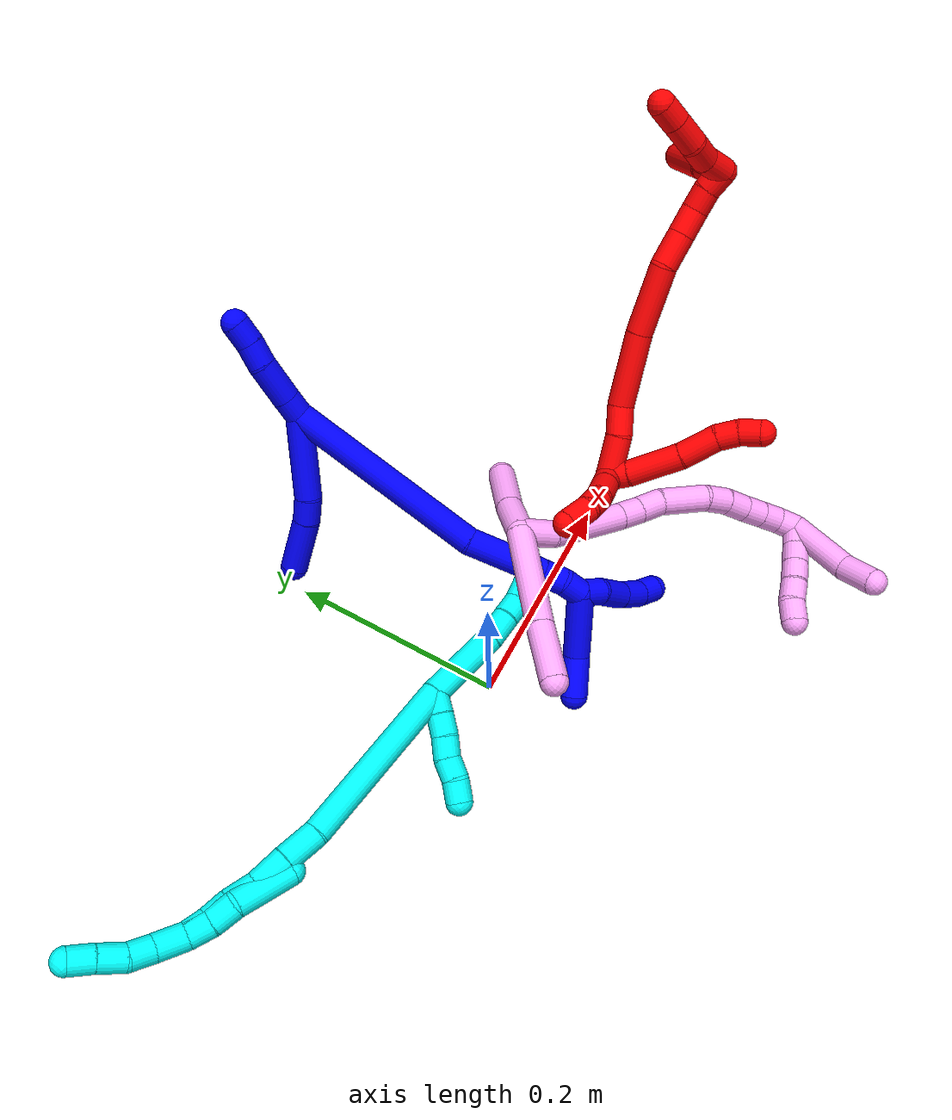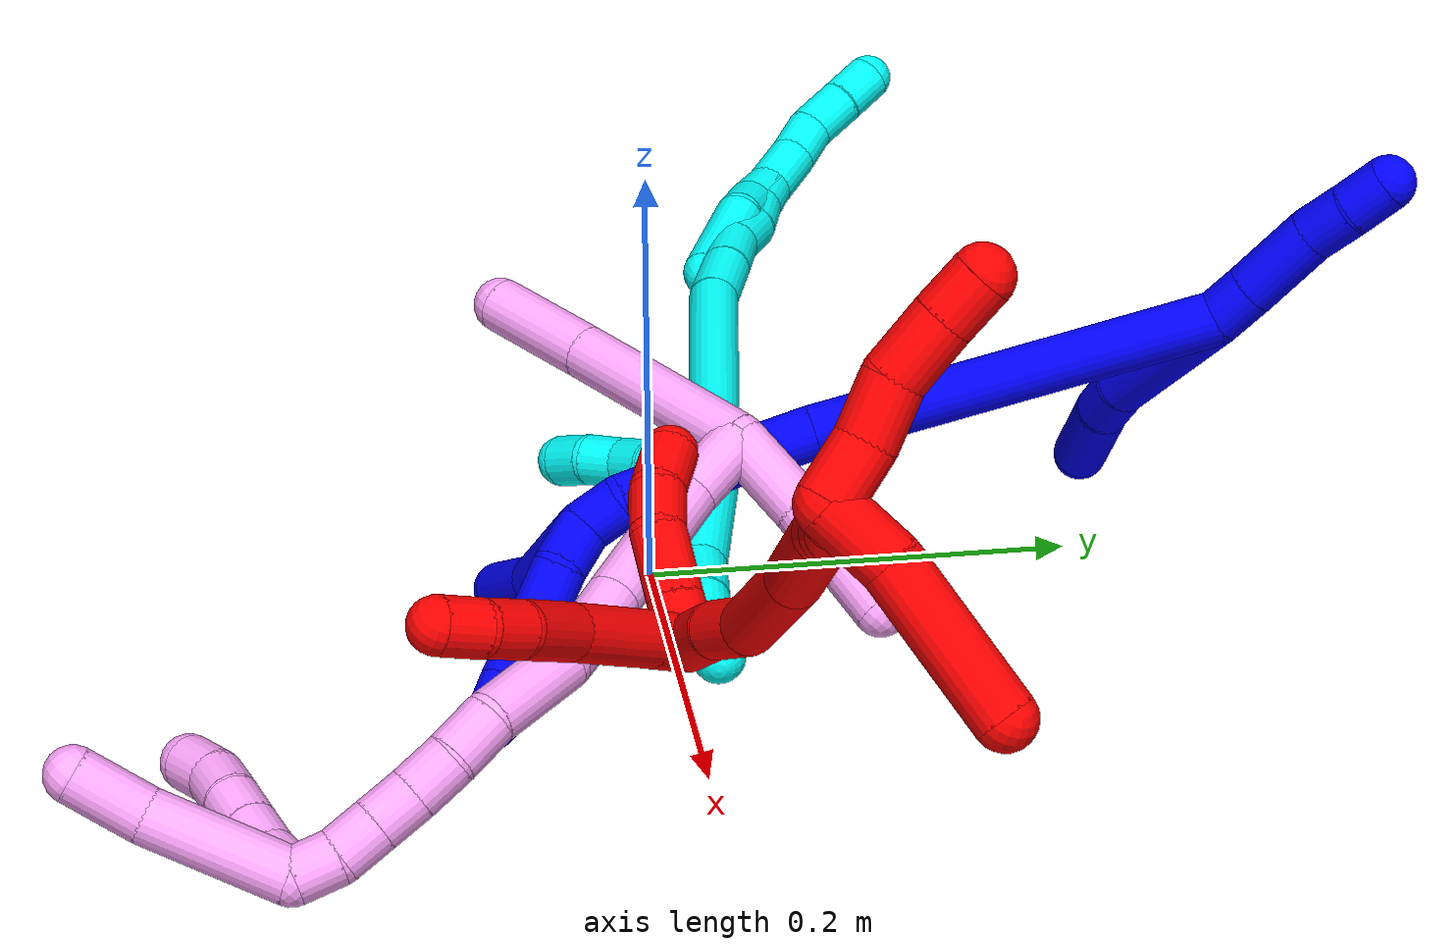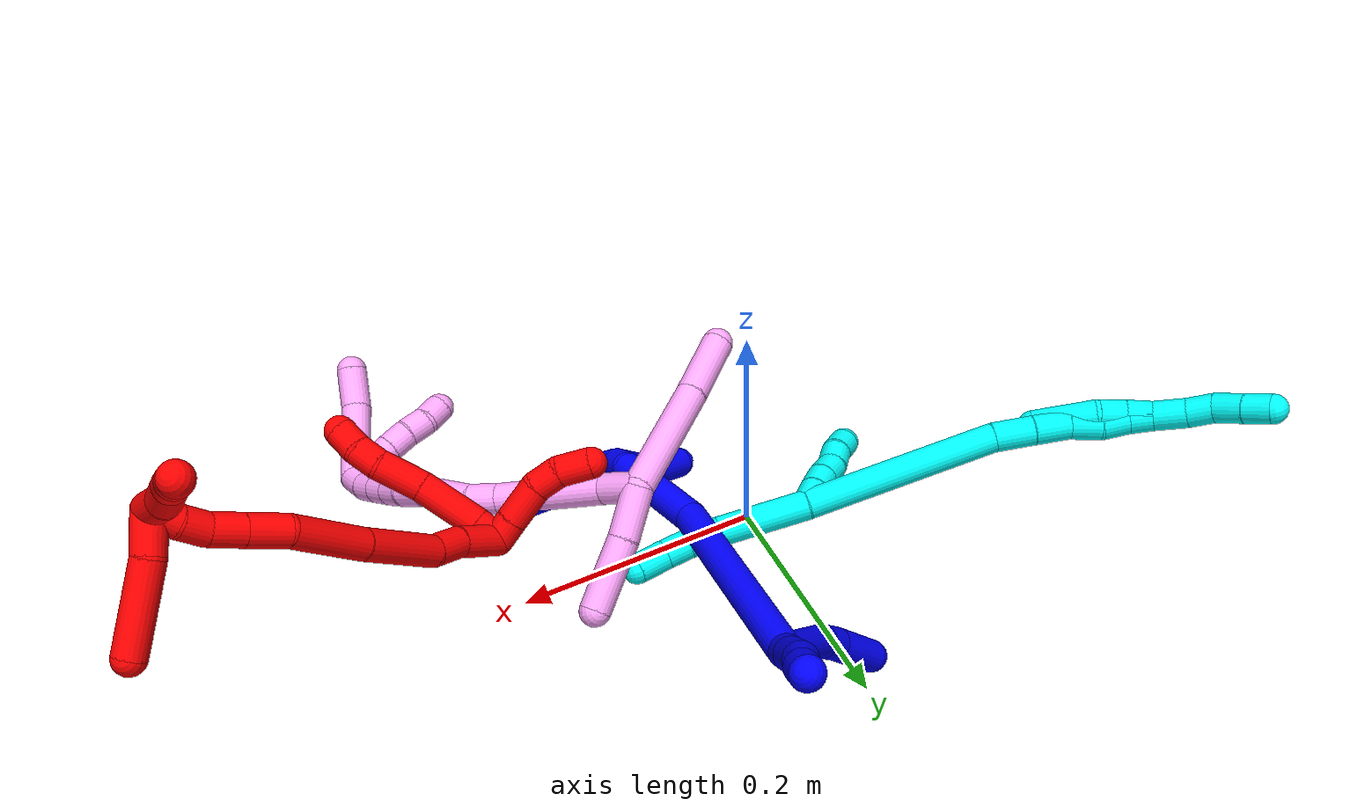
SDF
<sdf version="1.7">
 <world name="default">
  <plugin name="TubeGeneratorPlugin" filename="libtube_generator_plugin.so"/>
  <model name="photoneo_s_sensor">
   <static>1</static>
   <pose>0 0 2 1.57079 1.57079 3.14159</pose>
   <link name="link">
    <inertial><mass>0.1</mass></inertial>
    <sensor name="sensor" type="depth">
     <update_rate>30</update_rate>
     <camera>
      <horizontal_fov>1.22</horizontal_fov>
      <image><width>1920</width><height>1200</height><format>B8G8R8</format></image>
      <clip><near>0.1</near><far>4</far></clip>
      <depth_camera><output>points</output></depth_camera>
     </camera>
     <plugin name="camera_plugin" filename="libgazebo_ros_depth_camera.so">
      <baseline>0.2</baseline>
      <alwaysOn>1</alwaysOn>
      <updateRate>0.0</updateRate>
      <cameraName>camera_ir</cameraName>
      <imageTopicName>/camera/color/image_raw</imageTopicName>
      <cameraInfoTopicName>/camera/color/camera_info</cameraInfoTopicName>
      <depthImageTopicName>/camera/depth/image_raw</depthImageTopicName>
      <depthImageCameraInfoTopicName>/camera/depth/camera_info</depthImageCameraInfoTopicName>
      <pointCloudTopicName>/camera/depth/points</pointCloudTopicName>
      <frameName>fr_optical</frameName>
      <pointCloudCutoff>0.1</pointCloudCutoff>
      <pointCloudCutoffMax>2.0</pointCloudCutoffMax>
      <distortionK1>0</distortionK1>
      <distortionK2>0</distortionK2>
      <distortionK3>0</distortionK3>
      <distortionT1>0</distortionT1>
      <distortionT2>0</distortionT2>
      <CxPrime>0</CxPrime>
      <Cx>0</Cx>
      <Cy>0</Cy>
      <focalLength>0</focalLength>
      <hackBaseline>0</hackBaseline>
     </plugin>
    </sensor>
   </link>
  </model>
  <gravity>0 0 -9.8</gravity>
  <magnetic_field>6e-06 2.3e-05 -4.2e-05</magnetic_field>
  <atmosphere type="adiabatic"/>
  <physics name="default_physics" default="0" type="ode">
   <max_step_size>0.003</max_step_size>
   <real_time_factor>1</real_time_factor>
   <real_time_update_rate>1000</real_time_update_rate>
   <max_contacts>10000</max_contacts>
   <ode>
    <solver>
     <type>quick</type>
     <iters>100</iters>
     <sor>1.3</sor>
     <use_dynamic_moi_rescaling>0</use_dynamic_moi_rescaling>
    </solver>
    <constraints>
     <contact_max_correcting_vel>0</contact_max_correcting_vel>
     <contact_surface_layer>0.001</contact_surface_layer>
     <cfm>0</cfm>
     <erp>0.2</erp>
    </constraints>
   </ode>
  </physics>
  <scene><ambient>0.4 0.4 0.4 1</ambient><background>0.7 0.7 0.7 1</background><shadows>0</shadows></scene>
  <audio><device>default</device></audio>
  <spherical_coordinates>
   <surface_model>EARTH_WGS84</surface_model>
   <latitude_deg>0</latitude_deg>
   <longitude_deg>0</longitude_deg>
   <elevation>0</elevation>
   <heading_deg>0</heading_deg>
  </spherical_coordinates>
  <model name="bin">
   <static>1</static>
   <link name="bottom">
    <collision name="collision-bottom">
     <pose>0 0 -0.01 0 -0 0</pose>
     <geometry><box><size>0.8 0.6 0.02</size></box></geometry>
     <surface>
      <friction><ode><mu>100</mu><mu2>100</mu2></ode></friction>
      <contact><collide_bitmask>65535</collide_bitmask></contact>
     </surface>
    </collision>
   </link>
   <link name="west_wall">
    <collision name="collision-west_wall">
     <pose>-0.41 0 0.1 0 -0 0</pose>
     <geometry><box><size>0.02 0.6 0.2</size></box></geometry>
     <surface>
      <friction><ode><mu>100</mu><mu2>100</mu2></ode></friction>
      <contact><collide_bitmask>65535</collide_bitmask></contact>
     </surface>
    </collision>
   </link>
   <link name="east_wall">
    <collision name="collision-east_wall">
     <pose>0.41 0 0.1 0 -0 0</pose>
     <geometry><box><size>0.02 0.6 0.2</size></box></geometry>
     <surface>
      <friction><ode><mu>100</mu><mu2>100</mu2></ode></friction>
      <contact><collide_bitmask>65535</collide_bitmask></contact>
     </surface>
    </collision>
   </link>
   <link name="south_wall">
    <collision name="collision-south_wall">
     <pose>0 -0.31 0.1 0 -0 0</pose>
     <geometry><box><size>0.8 0.02 0.2</size></box></geometry>
     <surface>
      <friction><ode><mu>100</mu><mu2>100</mu2></ode></friction>
      <contact><collide_bitmask>65535</collide_bitmask></contact>
     </surface>
    </collision>
   </link>
   <link name="north_wall">
    <collision name="collision-north_wall">
     <pose>0 0.31 0.1 0 -0 0</pose>
     <geometry><box><size>0.8 0.02 0.2</size></box></geometry>
     <surface>
      <friction><ode><mu>100</mu><mu2>100</mu2></ode></friction>
      <contact><collide_bitmask>65535</collide_bitmask></contact>
     </surface>
    </collision>
   </link>
  </model>
  <model name="1">
   <static>0</static>
   <link name="1">
    <collision name="collision-cylinder-e_1_2_8">
     <pose>-0.003405 -0.006839 -0.03756 2.96149 -0.088949 -0.915842</pose>
     <geometry><cylinder><radius>0.0125</radius><length>0.076658</length></cylinder></geometry>
     <surface>
      <friction><ode><mu>1.16</mu><mu2>1.16</mu2><slip1>0</slip1><slip2>0</slip2></ode></friction>
      <contact><ode><kp>1e+06</kp><kd>1</kd><max_vel>0</max_vel><min_depth>0.001</min_depth></ode></contact>
     </surface>
    </collision>
    <visual name="visual-cylinder-e_1_2_8">
     <pose>-0.003405 -0.006839 -0.03756 2.96149 -0.088949 -0.915842</pose>
     <geometry><cylinder><radius>0.0125</radius><length>0.076658</length></cylinder></geometry>
     <material><ambient>0 0 1 1</ambient></material>
    </visual>
    <collision name="collision-cylinder-e_2_8_9">
     <pose>-0.007447 -0.013436 -0.086689 -3.12071 -0.055024 2.41632</pose>
     <geometry><cylinder><radius>0.0125</radius><length>0.023178</length></cylinder></geometry>
     <surface>
      <friction><ode><mu>1.16</mu><mu2>1.16</mu2><slip1>0</slip1><slip2>0</slip2></ode></friction>
      <contact><ode><kp>1e+06</kp><kd>1</kd><max_vel>0</max_vel><min_depth>0.001</min_depth></ode></contact>
     </surface>
    </collision>
    <visual name="visual-cylinder-e_2_8_9">
     <pose>-0.007447 -0.013436 -0.086689 -3.12071 -0.055024 2.41632</pose>
     <geometry><cylinder><radius>0.0125</radius><length>0.023178</length></cylinder></geometry>
     <material><ambient>0 0 1 1</ambient></material>
    </visual>
    <collision name="collision-cylinder-e_3_9_6">
     <pose>-0.009966 -0.008398 -0.122805 -2.94862 -0.075074 0.740277</pose>
     <geometry><cylinder><radius>0.0125</radius><length>0.050164</length></cylinder></geometry>
     <surface>
      <friction><ode><mu>1.16</mu><mu2>1.16</mu2><slip1>0</slip1><slip2>0</slip2></ode></friction>
      <contact><ode><kp>1e+06</kp><kd>1</kd><max_vel>0</max_vel><min_depth>0.001</min_depth></ode></contact>
     </surface>
    </collision>
    <visual name="visual-cylinder-e_3_9_6">
     <pose>-0.009966 -0.008398 -0.122805 -2.94862 -0.075074 0.740277</pose>
     <geometry><cylinder><radius>0.0125</radius><length>0.050164</length></cylinder></geometry>
     <material><ambient>0 0 1 1</ambient></material>
    </visual>
    <collision name="collision-cylinder-e_1_2_10">
     <pose>-0.002593 0.005342 0.008243 -0.574959 -0.258137 0.076712</pose>
     <geometry><cylinder><radius>0.0125</radius><length>0.020319</length></cylinder></geometry>
     <surface>
      <friction><ode><mu>1.16</mu><mu2>1.16</mu2><slip1>0</slip1><slip2>0</slip2></ode></friction>
      <contact><ode><kp>1e+06</kp><kd>1</kd><max_vel>0</max_vel><min_depth>0.001</min_depth></ode></contact>
     </surface>
    </collision>
    <visual name="visual-cylinder-e_1_2_10">
     <pose>-0.002593 0.005342 0.008243 -0.574959 -0.258137 0.076712</pose>
     <geometry><cylinder><radius>0.0125</radius><length>0.020319</length></cylinder></geometry>
     <material><ambient>0 0 1 1</ambient></material>
    </visual>
    <collision name="collision-cylinder-e_2_10_11">
     <pose>-0.010172 0.019956 0.031911 -0.5413 -0.270207 0.075395</pose>
     <geometry><cylinder><radius>0.0125</radius><length>0.037349</length></cylinder></geometry>
     <surface>
      <friction><ode><mu>1.16</mu><mu2>1.16</mu2><slip1>0</slip1><slip2>0</slip2></ode></friction>
      <contact><ode><kp>1e+06</kp><kd>1</kd><max_vel>0</max_vel><min_depth>0.001</min_depth></ode></contact>
     </surface>
    </collision>
    <visual name="visual-cylinder-e_2_10_11">
     <pose>-0.010172 0.019956 0.031911 -0.5413 -0.270207 0.075395</pose>
     <geometry><cylinder><radius>0.0125</radius><length>0.037349</length></cylinder></geometry>
     <material><ambient>0 0 1 1</ambient></material>
    </visual>
    <collision name="collision-cylinder-e_3_11_12">
     <pose>-0.016056 0.034698 0.056705 -0.528361 -0.082732 0.022391</pose>
     <geometry><cylinder><radius>0.0125</radius><length>0.021773</length></cylinder></geometry>
     <surface>
      <friction><ode><mu>1.16</mu><mu2>1.16</mu2><slip1>0</slip1><slip2>0</slip2></ode></friction>
      <contact><ode><kp>1e+06</kp><kd>1</kd><max_vel>0</max_vel><min_depth>0.001</min_depth></ode></contact>
     </surface>
    </collision>
    <visual name="visual-cylinder-e_3_11_12">
     <pose>-0.016056 0.034698 0.056705 -0.528361 -0.082732 0.022391</pose>
     <geometry><cylinder><radius>0.0125</radius><length>0.021773</length></cylinder></geometry>
     <material><ambient>0 0 1 1</ambient></material>
    </visual>
    <collision name="collision-cylinder-e_4_12_5">
     <pose>-0.018822 0.046057 0.074291 -0.621914 -0.182558 0.058818</pose>
     <geometry><cylinder><radius>0.0125</radius><length>0.020559</length></cylinder></geometry>
     <surface>
      <friction><ode><mu>1.16</mu><mu2>1.16</mu2><slip1>0</slip1><slip2>0</slip2></ode></friction>
      <contact><ode><kp>1e+06</kp><kd>1</kd><max_vel>0</max_vel><min_depth>0.001</min_depth></ode></contact>
     </surface>
    </collision>
    <visual name="visual-cylinder-e_4_12_5">
     <pose>-0.018822 0.046057 0.074291 -0.621914 -0.182558 0.058818</pose>
     <geometry><cylinder><radius>0.0125</radius><length>0.020559</length></cylinder></geometry>
     <material><ambient>0 0 1 1</ambient></material>
    </visual>
    <collision name="collision-cylinder-e_1_2_13">
     <pose>0.004398 -0.08212 -0.045089 2.07292 0.046907 0.07924</pose>
     <geometry><cylinder><radius>0.0125</radius><length>0.187575</length></cylinder></geometry>
     <surface>
      <friction><ode><mu>1.16</mu><mu2>1.16</mu2><slip1>0</slip1><slip2>0</slip2></ode></friction>
      <contact><ode><kp>1e+06</kp><kd>1</kd><max_vel>0</max_vel><min_depth>0.001</min_depth></ode></contact>
     </surface>
    </collision>
    <visual name="visual-cylinder-e_1_2_13">
     <pose>0.004398 -0.08212 -0.045089 2.07292 0.046907 0.07924</pose>
     <geometry><cylinder><radius>0.0125</radius><length>0.187575</length></cylinder></geometry>
     <material><ambient>0 0 1 1</ambient></material>
    </visual>
    <collision name="collision-cylinder-e_2_13_14">
     <pose>0.014165 -0.188273 -0.097991 1.88509 0.209364 0.287272</pose>
     <geometry><cylinder><radius>0.0125</radius><length>0.05167</length></cylinder></geometry>
     <surface>
      <friction><ode><mu>1.16</mu><mu2>1.16</mu2><slip1>0</slip1><slip2>0</slip2></ode></friction>
      <contact><ode><kp>1e+06</kp><kd>1</kd><max_vel>0</max_vel><min_depth>0.001</min_depth></ode></contact>
     </surface>
    </collision>
    <visual name="visual-cylinder-e_2_13_14">
     <pose>0.014165 -0.188273 -0.097991 1.88509 0.209364 0.287272</pose>
     <geometry><cylinder><radius>0.0125</radius><length>0.05167</length></cylinder></geometry>
     <material><ambient>0 0 1 1</ambient></material>
    </visual>
    <collision name="collision-cylinder-e_3_14_15">
     <pose>0.021581 -0.221595 -0.109204 1.92183 0.204062 0.290988</pose>
     <geometry><cylinder><radius>0.0125</radius><length>0.020203</length></cylinder></geometry>
     <surface>
      <friction><ode><mu>1.16</mu><mu2>1.16</mu2><slip1>0</slip1><slip2>0</slip2></ode></friction>
      <contact><ode><kp>1e+06</kp><kd>1</kd><max_vel>0</max_vel><min_depth>0.001</min_depth></ode></contact>
     </surface>
    </collision>
    <visual name="visual-cylinder-e_3_14_15">
     <pose>0.021581 -0.221595 -0.109204 1.92183 0.204062 0.290988</pose>
     <geometry><cylinder><radius>0.0125</radius><length>0.020203</length></cylinder></geometry>
     <material><ambient>0 0 1 1</ambient></material>
    </visual>
    <collision name="collision-cylinder-e_4_15_16">
     <pose>0.025864 -0.240231 -0.115928 1.91231 0.221627 0.312703</pose>
     <geometry><cylinder><radius>0.0125</radius><length>0.020338</length></cylinder></geometry>
     <surface>
      <friction><ode><mu>1.16</mu><mu2>1.16</mu2><slip1>0</slip1><slip2>0</slip2></ode></friction>
      <contact><ode><kp>1e+06</kp><kd>1</kd><max_vel>0</max_vel><min_depth>0.001</min_depth></ode></contact>
     </surface>
    </collision>
    <visual name="visual-cylinder-e_4_15_16">
     <pose>0.025864 -0.240231 -0.115928 1.91231 0.221627 0.312703</pose>
     <geometry><cylinder><radius>0.0125</radius><length>0.020338</length></cylinder></geometry>
     <material><ambient>0 0 1 1</ambient></material>
    </visual>
    <collision name="collision-cylinder-e_5_16_1">
     <pose>0.03152 -0.257153 -0.125001 2.22012 0.345338 0.675779</pose>
     <geometry><cylinder><radius>0.0125</radius><length>0.020214</length></cylinder></geometry>
     <surface>
      <friction><ode><mu>1.16</mu><mu2>1.16</mu2><slip1>0</slip1><slip2>0</slip2></ode></friction>
      <contact><ode><kp>1e+06</kp><kd>1</kd><max_vel>0</max_vel><min_depth>0.001</min_depth></ode></contact>
     </surface>
    </collision>
    <visual name="visual-cylinder-e_5_16_1">
     <pose>0.03152 -0.257153 -0.125001 2.22012 0.345338 0.675779</pose>
     <geometry><cylinder><radius>0.0125</radius><length>0.020214</length></cylinder></geometry>
     <material><ambient>0 0 1 1</ambient></material>
    </visual>
    <collision name="collision-cylinder-e_1_1_17">
     <pose>0.03271 -0.266622 -0.161558 3.08019 -0.072177 -1.73195</pose>
     <geometry><cylinder><radius>0.0125</radius><length>0.06189</length></cylinder></geometry>
     <surface>
      <friction><ode><mu>1.16</mu><mu2>1.16</mu2><slip1>0</slip1><slip2>0</slip2></ode></friction>
      <contact><ode><kp>1e+06</kp><kd>1</kd><max_vel>0</max_vel><min_depth>0.001</min_depth></ode></contact>
     </surface>
    </collision>
    <visual name="visual-cylinder-e_1_1_17">
     <pose>0.03271 -0.266622 -0.161558 3.08019 -0.072177 -1.73195</pose>
     <geometry><cylinder><radius>0.0125</radius><length>0.06189</length></cylinder></geometry>
     <material><ambient>0 0 1 1</ambient></material>
    </visual>
    <collision name="collision-cylinder-e_2_17_4">
     <pose>0.023385 -0.271298 -0.209829 2.98364 -0.381432 -2.36353</pose>
     <geometry><cylinder><radius>0.0125</radius><length>0.03811</length></cylinder></geometry>
     <surface>
      <friction><ode><mu>1.16</mu><mu2>1.16</mu2><slip1>0</slip1><slip2>0</slip2></ode></friction>
      <contact><ode><kp>1e+06</kp><kd>1</kd><max_vel>0</max_vel><min_depth>0.001</min_depth></ode></contact>
     </surface>
    </collision>
    <visual name="visual-cylinder-e_2_17_4">
     <pose>0.023385 -0.271298 -0.209829 2.98364 -0.381432 -2.36353</pose>
     <geometry><cylinder><radius>0.0125</radius><length>0.03811</length></cylinder></geometry>
     <material><ambient>0 0 1 1</ambient></material>
    </visual>
    <collision name="collision-cylinder-e_1_1_18">
     <pose>0.043856 -0.271275 -0.132752 1.86737 0.915927 1.17514</pose>
     <geometry><cylinder><radius>0.0125</radius><length>0.022479</length></cylinder></geometry>
     <surface>
      <friction><ode><mu>1.16</mu><mu2>1.16</mu2><slip1>0</slip1><slip2>0</slip2></ode></friction>
      <contact><ode><kp>1e+06</kp><kd>1</kd><max_vel>0</max_vel><min_depth>0.001</min_depth></ode></contact>
     </surface>
    </collision>
    <visual name="visual-cylinder-e_1_1_18">
     <pose>0.043856 -0.271275 -0.132752 1.86737 0.915927 1.17514</pose>
     <geometry><cylinder><radius>0.0125</radius><length>0.022479</length></cylinder></geometry>
     <material><ambient>0 0 1 1</ambient></material>
    </visual>
    <collision name="collision-cylinder-e_2_18_19">
     <pose>0.065259 -0.284528 -0.141349 2.34786 0.925222 1.74383</pose>
     <geometry><cylinder><radius>0.0125</radius><length>0.03127</length></cylinder></geometry>
     <surface>
      <friction><ode><mu>1.16</mu><mu2>1.16</mu2><slip1>0</slip1><slip2>0</slip2></ode></friction>
      <contact><ode><kp>1e+06</kp><kd>1</kd><max_vel>0</max_vel><min_depth>0.001</min_depth></ode></contact>
     </surface>
    </collision>
    <visual name="visual-cylinder-e_2_18_19">
     <pose>0.065259 -0.284528 -0.141349 2.34786 0.925222 1.74383</pose>
     <geometry><cylinder><radius>0.0125</radius><length>0.03127</length></cylinder></geometry>
     <material><ambient>0 0 1 1</ambient></material>
    </visual>
    <collision name="collision-cylinder-e_3_19_20">
     <pose>0.088719 -0.297533 -0.151362 2.06794 0.992283 1.47615</pose>
     <geometry><cylinder><radius>0.0125</radius><length>0.026207</length></cylinder></geometry>
     <surface>
      <friction><ode><mu>1.16</mu><mu2>1.16</mu2><slip1>0</slip1><slip2>0</slip2></ode></friction>
      <contact><ode><kp>1e+06</kp><kd>1</kd><max_vel>0</max_vel><min_depth>0.001</min_depth></ode></contact>
     </surface>
    </collision>
    <visual name="visual-cylinder-e_3_19_20">
     <pose>0.088719 -0.297533 -0.151362 2.06794 0.992283 1.47615</pose>
     <geometry><cylinder><radius>0.0125</radius><length>0.026207</length></cylinder></geometry>
     <material><ambient>0 0 1 1</ambient></material>
    </visual>
    <collision name="collision-cylinder-e_4_20_3">
     <pose>0.108488 -0.308583 -0.155446 1.71032 1.07138 1.19813</pose>
     <geometry><cylinder><radius>0.0125</radius><length>0.020044</length></cylinder></geometry>
     <surface>
      <friction><ode><mu>1.16</mu><mu2>1.16</mu2><slip1>0</slip1><slip2>0</slip2></ode></friction>
      <contact><ode><kp>1e+06</kp><kd>1</kd><max_vel>0</max_vel><min_depth>0.001</min_depth></ode></contact>
     </surface>
    </collision>
    <visual name="visual-cylinder-e_4_20_3">
     <pose>0.108488 -0.308583 -0.155446 1.71032 1.07138 1.19813</pose>
     <geometry><cylinder><radius>0.0125</radius><length>0.020044</length></cylinder></geometry>
     <material><ambient>0 0 1 1</ambient></material>
    </visual>
    <collision name="collision-sphere-3">
     <pose>0.117286 -0.313336 -0.156114 0 -0 0</pose>
     <geometry><sphere><radius>0.0125</radius></sphere></geometry>
     <surface>
      <friction><ode><mu>1.16</mu><mu2>1.16</mu2><slip1>0</slip1><slip2>0</slip2></ode></friction>
      <contact><ode><kp>1e+06</kp><kd>1</kd><max_vel>0</max_vel><min_depth>0.001</min_depth></ode></contact>
     </surface>
    </collision>
    <visual name="visual-sphere-3">
     <pose>0.117286 -0.313336 -0.156114 0 -0 0</pose>
     <geometry><sphere><radius>0.0125</radius></sphere></geometry>
     <material><ambient>0 0 1 1</ambient></material>
    </visual>
    <collision name="collision-sphere-20">
     <pose>0.09969 -0.30383 -0.154779 0 -0 0</pose>
     <geometry><sphere><radius>0.0125</radius></sphere></geometry>
     <surface>
      <friction><ode><mu>1.16</mu><mu2>1.16</mu2><slip1>0</slip1><slip2>0</slip2></ode></friction>
      <contact><ode><kp>1e+06</kp><kd>1</kd><max_vel>0</max_vel><min_depth>0.001</min_depth></ode></contact>
     </surface>
    </collision>
    <visual name="visual-sphere-20">
     <pose>0.09969 -0.30383 -0.154779 0 -0 0</pose>
     <geometry><sphere><radius>0.0125</radius></sphere></geometry>
     <material><ambient>0 0 1 1</ambient></material>
    </visual>
    <collision name="collision-sphere-19">
     <pose>0.077747 -0.291235 -0.147945 0 -0 0</pose>
     <geometry><sphere><radius>0.0125</radius></sphere></geometry>
     <surface>
      <friction><ode><mu>1.16</mu><mu2>1.16</mu2><slip1>0</slip1><slip2>0</slip2></ode></friction>
      <contact><ode><kp>1e+06</kp><kd>1</kd><max_vel>0</max_vel><min_depth>0.001</min_depth></ode></contact>
     </surface>
    </collision>
    <visual name="visual-sphere-19">
     <pose>0.077747 -0.291235 -0.147945 0 -0 0</pose>
     <geometry><sphere><radius>0.0125</radius></sphere></geometry>
     <material><ambient>0 0 1 1</ambient></material>
    </visual>
    <collision name="collision-sphere-11">
     <pose>-0.015157 0.029229 0.047335 0 -0 0</pose>
     <geometry><sphere><radius>0.0125</radius></sphere></geometry>
     <surface>
      <friction><ode><mu>1.16</mu><mu2>1.16</mu2><slip1>0</slip1><slip2>0</slip2></ode></friction>
      <contact><ode><kp>1e+06</kp><kd>1</kd><max_vel>0</max_vel><min_depth>0.001</min_depth></ode></contact>
     </surface>
    </collision>
    <visual name="visual-sphere-11">
     <pose>-0.015157 0.029229 0.047335 0 -0 0</pose>
     <geometry><sphere><radius>0.0125</radius></sphere></geometry>
     <material><ambient>0 0 1 1</ambient></material>
    </visual>
    <collision name="collision-sphere-10">
     <pose>-0.005187 0.010683 0.016487 0 -0 0</pose>
     <geometry><sphere><radius>0.0125</radius></sphere></geometry>
     <surface>
      <friction><ode><mu>1.16</mu><mu2>1.16</mu2><slip1>0</slip1><slip2>0</slip2></ode></friction>
      <contact><ode><kp>1e+06</kp><kd>1</kd><max_vel>0</max_vel><min_depth>0.001</min_depth></ode></contact>
     </surface>
    </collision>
    <visual name="visual-sphere-10">
     <pose>-0.005187 0.010683 0.016487 0 -0 0</pose>
     <geometry><sphere><radius>0.0125</radius></sphere></geometry>
     <material><ambient>0 0 1 1</ambient></material>
    </visual>
    <collision name="collision-sphere-6">
     <pose>-0.011847 -0.003601 -0.147352 0 -0 0</pose>
     <geometry><sphere><radius>0.0125</radius></sphere></geometry>
     <surface>
      <friction><ode><mu>1.16</mu><mu2>1.16</mu2><slip1>0</slip1><slip2>0</slip2></ode></friction>
      <contact><ode><kp>1e+06</kp><kd>1</kd><max_vel>0</max_vel><min_depth>0.001</min_depth></ode></contact>
     </surface>
    </collision>
    <visual name="visual-sphere-6">
     <pose>-0.011847 -0.003601 -0.147352 0 -0 0</pose>
     <geometry><sphere><radius>0.0125</radius></sphere></geometry>
     <material><ambient>0 0 1 1</ambient></material>
    </visual>
    <collision name="collision-sphere-9">
     <pose>-0.008084 -0.013195 -0.098257 0 -0 0</pose>
     <geometry><sphere><radius>0.0125</radius></sphere></geometry>
     <surface>
      <friction><ode><mu>1.16</mu><mu2>1.16</mu2><slip1>0</slip1><slip2>0</slip2></ode></friction>
      <contact><ode><kp>1e+06</kp><kd>1</kd><max_vel>0</max_vel><min_depth>0.001</min_depth></ode></contact>
     </surface>
    </collision>
    <visual name="visual-sphere-9">
     <pose>-0.008084 -0.013195 -0.098257 0 -0 0</pose>
     <geometry><sphere><radius>0.0125</radius></sphere></geometry>
     <material><ambient>0 0 1 1</ambient></material>
    </visual>
    <collision name="collision-sphere-2">
     <geometry><sphere><radius>0.0125</radius></sphere></geometry>
     <surface>
      <friction><ode><mu>1.16</mu><mu2>1.16</mu2><slip1>0</slip1><slip2>0</slip2></ode></friction>
      <contact><ode><kp>1e+06</kp><kd>1</kd><max_vel>0</max_vel><min_depth>0.001</min_depth></ode></contact>
     </surface>
    </collision>
    <visual name="visual-sphere-2">
     <geometry><sphere><radius>0.0125</radius></sphere></geometry>
     <material><ambient>0 0 1 1</ambient></material>
    </visual>
    <collision name="collision-sphere-8">
     <pose>-0.00681 -0.013678 -0.07512 0 -0 0</pose>
     <geometry><sphere><radius>0.0125</radius></sphere></geometry>
     <surface>
      <friction><ode><mu>1.16</mu><mu2>1.16</mu2><slip1>0</slip1><slip2>0</slip2></ode></friction>
      <contact><ode><kp>1e+06</kp><kd>1</kd><max_vel>0</max_vel><min_depth>0.001</min_depth></ode></contact>
     </surface>
    </collision>
    <visual name="visual-sphere-8">
     <pose>-0.00681 -0.013678 -0.07512 0 -0 0</pose>
     <geometry><sphere><radius>0.0125</radius></sphere></geometry>
     <material><ambient>0 0 1 1</ambient></material>
    </visual>
    <collision name="collision-sphere-12">
     <pose>-0.016956 0.040168 0.066074 0 -0 0</pose>
     <geometry><sphere><radius>0.0125</radius></sphere></geometry>
     <surface>
      <friction><ode><mu>1.16</mu><mu2>1.16</mu2><slip1>0</slip1><slip2>0</slip2></ode></friction>
      <contact><ode><kp>1e+06</kp><kd>1</kd><max_vel>0</max_vel><min_depth>0.001</min_depth></ode></contact>
     </surface>
    </collision>
    <visual name="visual-sphere-12">
     <pose>-0.016956 0.040168 0.066074 0 -0 0</pose>
     <geometry><sphere><radius>0.0125</radius></sphere></geometry>
     <material><ambient>0 0 1 1</ambient></material>
    </visual>
    <collision name="collision-sphere-5">
     <pose>-0.020688 0.051946 0.082507 0 -0 0</pose>
     <geometry><sphere><radius>0.0125</radius></sphere></geometry>
     <surface>
      <friction><ode><mu>1.16</mu><mu2>1.16</mu2><slip1>0</slip1><slip2>0</slip2></ode></friction>
      <contact><ode><kp>1e+06</kp><kd>1</kd><max_vel>0</max_vel><min_depth>0.001</min_depth></ode></contact>
     </surface>
    </collision>
    <visual name="visual-sphere-5">
     <pose>-0.020688 0.051946 0.082507 0 -0 0</pose>
     <geometry><sphere><radius>0.0125</radius></sphere></geometry>
     <material><ambient>0 0 1 1</ambient></material>
    </visual>
    <collision name="collision-sphere-13">
     <pose>0.008795 -0.16424 -0.090178 0 -0 0</pose>
     <geometry><sphere><radius>0.0125</radius></sphere></geometry>
     <surface>
      <friction><ode><mu>1.16</mu><mu2>1.16</mu2><slip1>0</slip1><slip2>0</slip2></ode></friction>
      <contact><ode><kp>1e+06</kp><kd>1</kd><max_vel>0</max_vel><min_depth>0.001</min_depth></ode></contact>
     </surface>
    </collision>
    <visual name="visual-sphere-13">
     <pose>0.008795 -0.16424 -0.090178 0 -0 0</pose>
     <geometry><sphere><radius>0.0125</radius></sphere></geometry>
     <material><ambient>0 0 1 1</ambient></material>
    </visual>
    <collision name="collision-sphere-14">
     <pose>0.019534 -0.212306 -0.105803 0 -0 0</pose>
     <geometry><sphere><radius>0.0125</radius></sphere></geometry>
     <surface>
      <friction><ode><mu>1.16</mu><mu2>1.16</mu2><slip1>0</slip1><slip2>0</slip2></ode></friction>
      <contact><ode><kp>1e+06</kp><kd>1</kd><max_vel>0</max_vel><min_depth>0.001</min_depth></ode></contact>
     </surface>
    </collision>
    <visual name="visual-sphere-14">
     <pose>0.019534 -0.212306 -0.105803 0 -0 0</pose>
     <geometry><sphere><radius>0.0125</radius></sphere></geometry>
     <material><ambient>0 0 1 1</ambient></material>
    </visual>
    <collision name="collision-sphere-15">
     <pose>0.023628 -0.230884 -0.112606 0 -0 0</pose>
     <geometry><sphere><radius>0.0125</radius></sphere></geometry>
     <surface>
      <friction><ode><mu>1.16</mu><mu2>1.16</mu2><slip1>0</slip1><slip2>0</slip2></ode></friction>
      <contact><ode><kp>1e+06</kp><kd>1</kd><max_vel>0</max_vel><min_depth>0.001</min_depth></ode></contact>
     </surface>
    </collision>
    <visual name="visual-sphere-15">
     <pose>0.023628 -0.230884 -0.112606 0 -0 0</pose>
     <geometry><sphere><radius>0.0125</radius></sphere></geometry>
     <material><ambient>0 0 1 1</ambient></material>
    </visual>
    <collision name="collision-sphere-16">
     <pose>0.028099 -0.249579 -0.119251 0 -0 0</pose>
     <geometry><sphere><radius>0.0125</radius></sphere></geometry>
     <surface>
      <friction><ode><mu>1.16</mu><mu2>1.16</mu2><slip1>0</slip1><slip2>0</slip2></ode></friction>
      <contact><ode><kp>1e+06</kp><kd>1</kd><max_vel>0</max_vel><min_depth>0.001</min_depth></ode></contact>
     </surface>
    </collision>
    <visual name="visual-sphere-16">
     <pose>0.028099 -0.249579 -0.119251 0 -0 0</pose>
     <geometry><sphere><radius>0.0125</radius></sphere></geometry>
     <material><ambient>0 0 1 1</ambient></material>
    </visual>
    <collision name="collision-sphere-1">
     <pose>0.034942 -0.264728 -0.130751 0 -0 0</pose>
     <geometry><sphere><radius>0.0125</radius></sphere></geometry>
     <surface>
      <friction><ode><mu>1.16</mu><mu2>1.16</mu2><slip1>0</slip1><slip2>0</slip2></ode></friction>
      <contact><ode><kp>1e+06</kp><kd>1</kd><max_vel>0</max_vel><min_depth>0.001</min_depth></ode></contact>
     </surface>
    </collision>
    <visual name="visual-sphere-1">
     <pose>0.034942 -0.264728 -0.130751 0 -0 0</pose>
     <geometry><sphere><radius>0.0125</radius></sphere></geometry>
     <material><ambient>0 0 1 1</ambient></material>
    </visual>
    <collision name="collision-sphere-18">
     <pose>0.05277 -0.277821 -0.134752 0 -0 0</pose>
     <geometry><sphere><radius>0.0125</radius></sphere></geometry>
     <surface>
      <friction><ode><mu>1.16</mu><mu2>1.16</mu2><slip1>0</slip1><slip2>0</slip2></ode></friction>
      <contact><ode><kp>1e+06</kp><kd>1</kd><max_vel>0</max_vel><min_depth>0.001</min_depth></ode></contact>
     </surface>
    </collision>
    <visual name="visual-sphere-18">
     <pose>0.05277 -0.277821 -0.134752 0 -0 0</pose>
     <geometry><sphere><radius>0.0125</radius></sphere></geometry>
     <material><ambient>0 0 1 1</ambient></material>
    </visual>
    <collision name="collision-sphere-17">
     <pose>0.030479 -0.268516 -0.192364 0 -0 0</pose>
     <geometry><sphere><radius>0.0125</radius></sphere></geometry>
     <surface>
      <friction><ode><mu>1.16</mu><mu2>1.16</mu2><slip1>0</slip1><slip2>0</slip2></ode></friction>
      <contact><ode><kp>1e+06</kp><kd>1</kd><max_vel>0</max_vel><min_depth>0.001</min_depth></ode></contact>
     </surface>
    </collision>
    <visual name="visual-sphere-17">
     <pose>0.030479 -0.268516 -0.192364 0 -0 0</pose>
     <geometry><sphere><radius>0.0125</radius></sphere></geometry>
     <material><ambient>0 0 1 1</ambient></material>
    </visual>
    <collision name="collision-sphere-4">
     <pose>0.016292 -0.27408 -0.227295 0 -0 0</pose>
     <geometry><sphere><radius>0.0125</radius></sphere></geometry>
     <surface>
      <friction><ode><mu>1.16</mu><mu2>1.16</mu2><slip1>0</slip1><slip2>0</slip2></ode></friction>
      <contact><ode><kp>1e+06</kp><kd>1</kd><max_vel>0</max_vel><min_depth>0.001</min_depth></ode></contact>
     </surface>
    </collision>
    <visual name="visual-sphere-4">
     <pose>0.016292 -0.27408 -0.227295 0 -0 0</pose>
     <geometry><sphere><radius>0.0125</radius></sphere></geometry>
     <material><ambient>0 0 1 1</ambient></material>
    </visual>
    <inertial>
     <pose>0.015327 -0.125615 -0.080028 0 -0 0</pose>
     <mass>0.75</mass>
     <inertia>
      <ixx>0.000619</ixx>
      <ixy>0</ixy>
      <ixz>0</ixz>
      <iyy>-0.000292</iyy>
      <iyz>0</iyz>
      <izz>0.000459</izz>
     </inertia>
    </inertial>
   </link>
   <pose>0.097218 0.244116 0.157547 -0.190029 0.653061 0.068048</pose>
  </model>
  <model name="2">
   <static>0</static>
   <link name="2">
    <collision name="collision-cylinder-e_1_2_8">
     <pose>0.00474 -0.008796 0.002156 1.33038 0.482184 0.381073</pose>
     <geometry><cylinder><radius>0.0125</radius><length>0.020443</length></cylinder></geometry>
     <surface>
      <friction><ode><mu>1.16</mu><mu2>1.16</mu2><slip1>0</slip1><slip2>0</slip2></ode></friction>
      <contact><ode><kp>1e+06</kp><kd>1</kd><max_vel>0</max_vel><min_depth>0.001</min_depth></ode></contact>
     </surface>
    </collision>
    <visual name="visual-cylinder-e_1_2_8">
     <pose>0.00474 -0.008796 0.002156 1.33038 0.482184 0.381073</pose>
     <geometry><cylinder><radius>0.0125</radius><length>0.020443</length></cylinder></geometry>
     <material><ambient>1 0 0 1</ambient></material>
    </visual>
    <collision name="collision-cylinder-e_2_8_9">
     <pose>0.02344 -0.037795 0.012237 1.19704 0.571635 0.395568</pose>
     <geometry><cylinder><radius>0.0125</radius><length>0.051609</length></cylinder></geometry>
     <surface>
      <friction><ode><mu>1.16</mu><mu2>1.16</mu2><slip1>0</slip1><slip2>0</slip2></ode></friction>
      <contact><ode><kp>1e+06</kp><kd>1</kd><max_vel>0</max_vel><min_depth>0.001</min_depth></ode></contact>
     </surface>
    </collision>
    <visual name="visual-cylinder-e_2_8_9">
     <pose>0.02344 -0.037795 0.012237 1.19704 0.571635 0.395568</pose>
     <geometry><cylinder><radius>0.0125</radius><length>0.051609</length></cylinder></geometry>
     <material><ambient>1 0 0 1</ambient></material>
    </visual>
    <collision name="collision-cylinder-e_3_9_10">
     <pose>0.048675 -0.070449 0.027452 1.04099 0.663289 0.38978</pose>
     <geometry><cylinder><radius>0.0125</radius><length>0.036621</length></cylinder></geometry>
     <surface>
      <friction><ode><mu>1.16</mu><mu2>1.16</mu2><slip1>0</slip1><slip2>0</slip2></ode></friction>
      <contact><ode><kp>1e+06</kp><kd>1</kd><max_vel>0</max_vel><min_depth>0.001</min_depth></ode></contact>
     </surface>
    </collision>
    <visual name="visual-cylinder-e_3_9_10">
     <pose>0.048675 -0.070449 0.027452 1.04099 0.663289 0.38978</pose>
     <geometry><cylinder><radius>0.0125</radius><length>0.036621</length></cylinder></geometry>
     <material><ambient>1 0 0 1</ambient></material>
    </visual>
    <collision name="collision-cylinder-e_4_10_11">
     <pose>0.065453 -0.091426 0.036932 1.31953 0.558816 0.437994</pose>
     <geometry><cylinder><radius>0.0125</radius><length>0.020766</length></cylinder></geometry>
     <surface>
      <friction><ode><mu>1.16</mu><mu2>1.16</mu2><slip1>0</slip1><slip2>0</slip2></ode></friction>
      <contact><ode><kp>1e+06</kp><kd>1</kd><max_vel>0</max_vel><min_depth>0.001</min_depth></ode></contact>
     </surface>
    </collision>
    <visual name="visual-cylinder-e_4_10_11">
     <pose>0.065453 -0.091426 0.036932 1.31953 0.558816 0.437994</pose>
     <geometry><cylinder><radius>0.0125</radius><length>0.020766</length></cylinder></geometry>
     <material><ambient>1 0 0 1</ambient></material>
    </visual>
    <collision name="collision-cylinder-e_5_11_6">
     <pose>0.074817 -0.109473 0.039546 1.52622 0.384709 0.368318</pose>
     <geometry><cylinder><radius>0.0125</radius><length>0.020561</length></cylinder></geometry>
     <surface>
      <friction><ode><mu>1.16</mu><mu2>1.16</mu2><slip1>0</slip1><slip2>0</slip2></ode></friction>
      <contact><ode><kp>1e+06</kp><kd>1</kd><max_vel>0</max_vel><min_depth>0.001</min_depth></ode></contact>
     </surface>
    </collision>
    <visual name="visual-cylinder-e_5_11_6">
     <pose>0.074817 -0.109473 0.039546 1.52622 0.384709 0.368318</pose>
     <geometry><cylinder><radius>0.0125</radius><length>0.020561</length></cylinder></geometry>
     <material><ambient>1 0 0 1</ambient></material>
    </visual>
    <collision name="collision-cylinder-e_1_2_12">
     <pose>-0.008763 -0.004599 0.00241 1.08813 -1.03596 -0.663999</pose>
     <geometry><cylinder><radius>0.0125</radius><length>0.020371</length></cylinder></geometry>
     <surface>
      <friction><ode><mu>1.16</mu><mu2>1.16</mu2><slip1>0</slip1><slip2>0</slip2></ode></friction>
      <contact><ode><kp>1e+06</kp><kd>1</kd><max_vel>0</max_vel><min_depth>0.001</min_depth></ode></contact>
     </surface>
    </collision>
    <visual name="visual-cylinder-e_1_2_12">
     <pose>-0.008763 -0.004599 0.00241 1.08813 -1.03596 -0.663999</pose>
     <geometry><cylinder><radius>0.0125</radius><length>0.020371</length></cylinder></geometry>
     <material><ambient>1 0 0 1</ambient></material>
    </visual>
    <collision name="collision-cylinder-e_2_12_13">
     <pose>-0.03148 -0.016183 0.008685 1.06538 -1.05104 -0.658848</pose>
     <geometry><cylinder><radius>0.0125</radius><length>0.032153</length></cylinder></geometry>
     <surface>
      <friction><ode><mu>1.16</mu><mu2>1.16</mu2><slip1>0</slip1><slip2>0</slip2></ode></friction>
      <contact><ode><kp>1e+06</kp><kd>1</kd><max_vel>0</max_vel><min_depth>0.001</min_depth></ode></contact>
     </surface>
    </collision>
    <visual name="visual-cylinder-e_2_12_13">
     <pose>-0.03148 -0.016183 0.008685 1.06538 -1.05104 -0.658848</pose>
     <geometry><cylinder><radius>0.0125</radius><length>0.032153</length></cylinder></geometry>
     <material><ambient>1 0 0 1</ambient></material>
    </visual>
    <collision name="collision-cylinder-e_3_13_14">
     <pose>-0.055857 -0.024777 0.01387 0.883674 -1.3739 -0.740216</pose>
     <geometry><cylinder><radius>0.0125</radius><length>0.021258</length></cylinder></geometry>
     <surface>
      <friction><ode><mu>1.16</mu><mu2>1.16</mu2><slip1>0</slip1><slip2>0</slip2></ode></friction>
      <contact><ode><kp>1e+06</kp><kd>1</kd><max_vel>0</max_vel><min_depth>0.001</min_depth></ode></contact>
     </surface>
    </collision>
    <visual name="visual-cylinder-e_3_13_14">
     <pose>-0.055857 -0.024777 0.01387 0.883674 -1.3739 -0.740216</pose>
     <geometry><cylinder><radius>0.0125</radius><length>0.021258</length></cylinder></geometry>
     <material><ambient>1 0 0 1</ambient></material>
    </visual>
    <collision name="collision-cylinder-e_4_14_5">
     <pose>-0.079247 -0.024501 0.014781 -1.78401 -1.42321 1.63746</pose>
     <geometry><cylinder><radius>0.0125</radius><length>0.026218</length></cylinder></geometry>
     <surface>
      <friction><ode><mu>1.16</mu><mu2>1.16</mu2><slip1>0</slip1><slip2>0</slip2></ode></friction>
      <contact><ode><kp>1e+06</kp><kd>1</kd><max_vel>0</max_vel><min_depth>0.001</min_depth></ode></contact>
     </surface>
    </collision>
    <visual name="visual-cylinder-e_4_14_5">
     <pose>-0.079247 -0.024501 0.014781 -1.78401 -1.42321 1.63746</pose>
     <geometry><cylinder><radius>0.0125</radius><length>0.026218</length></cylinder></geometry>
     <material><ambient>1 0 0 1</ambient></material>
    </visual>
    <collision name="collision-cylinder-e_1_2_15">
     <pose>0.010739 -5.9e-05 0.016848 0.003511 0.567475 0.001024</pose>
     <geometry><cylinder><radius>0.0125</radius><length>0.03996</length></cylinder></geometry>
     <surface>
      <friction><ode><mu>1.16</mu><mu2>1.16</mu2><slip1>0</slip1><slip2>0</slip2></ode></friction>
      <contact><ode><kp>1e+06</kp><kd>1</kd><max_vel>0</max_vel><min_depth>0.001</min_depth></ode></contact>
     </surface>
    </collision>
    <visual name="visual-cylinder-e_1_2_15">
     <pose>0.010739 -5.9e-05 0.016848 0.003511 0.567475 0.001024</pose>
     <geometry><cylinder><radius>0.0125</radius><length>0.03996</length></cylinder></geometry>
     <material><ambient>1 0 0 1</ambient></material>
    </visual>
    <collision name="collision-cylinder-e_2_15_16">
     <pose>0.028866 0.002968 0.04516 -0.262992 0.556603 -0.075541</pose>
     <geometry><cylinder><radius>0.0125</radius><length>0.027965</length></cylinder></geometry>
     <surface>
      <friction><ode><mu>1.16</mu><mu2>1.16</mu2><slip1>0</slip1><slip2>0</slip2></ode></friction>
      <contact><ode><kp>1e+06</kp><kd>1</kd><max_vel>0</max_vel><min_depth>0.001</min_depth></ode></contact>
     </surface>
    </collision>
    <visual name="visual-cylinder-e_2_15_16">
     <pose>0.028866 0.002968 0.04516 -0.262992 0.556603 -0.075541</pose>
     <geometry><cylinder><radius>0.0125</radius><length>0.027965</length></cylinder></geometry>
     <material><ambient>1 0 0 1</ambient></material>
    </visual>
    <collision name="collision-cylinder-e_3_16_17">
     <pose>0.051417 0.00336 0.087916 0.085899 0.449807 0.019663</pose>
     <geometry><cylinder><radius>0.0125</radius><length>0.069755</length></cylinder></geometry>
     <surface>
      <friction><ode><mu>1.16</mu><mu2>1.16</mu2><slip1>0</slip1><slip2>0</slip2></ode></friction>
      <contact><ode><kp>1e+06</kp><kd>1</kd><max_vel>0</max_vel><min_depth>0.001</min_depth></ode></contact>
     </surface>
    </collision>
    <visual name="visual-cylinder-e_3_16_17">
     <pose>0.051417 0.00336 0.087916 0.085899 0.449807 0.019663</pose>
     <geometry><cylinder><radius>0.0125</radius><length>0.069755</length></cylinder></geometry>
     <material><ambient>1 0 0 1</ambient></material>
    </visual>
    <collision name="collision-cylinder-e_4_17_18">
     <pose>0.081375 -0.004791 0.147069 0.193411 0.480386 0.04751</pose>
     <geometry><cylinder><radius>0.0125</radius><length>0.064026</length></cylinder></geometry>
     <surface>
      <friction><ode><mu>1.16</mu><mu2>1.16</mu2><slip1>0</slip1><slip2>0</slip2></ode></friction>
      <contact><ode><kp>1e+06</kp><kd>1</kd><max_vel>0</max_vel><min_depth>0.001</min_depth></ode></contact>
     </surface>
    </collision>
    <visual name="visual-cylinder-e_4_17_18">
     <pose>0.081375 -0.004791 0.147069 0.193411 0.480386 0.04751</pose>
     <geometry><cylinder><radius>0.0125</radius><length>0.064026</length></cylinder></geometry>
     <material><ambient>1 0 0 1</ambient></material>
    </visual>
    <collision name="collision-cylinder-e_5_18_19">
     <pose>0.107314 -0.012885 0.185717 0.239748 0.787183 0.099954</pose>
     <geometry><cylinder><radius>0.0125</radius><length>0.031467</length></cylinder></geometry>
     <surface>
      <friction><ode><mu>1.16</mu><mu2>1.16</mu2><slip1>0</slip1><slip2>0</slip2></ode></friction>
      <contact><ode><kp>1e+06</kp><kd>1</kd><max_vel>0</max_vel><min_depth>0.001</min_depth></ode></contact>
     </surface>
    </collision>
    <visual name="visual-cylinder-e_5_18_19">
     <pose>0.107314 -0.012885 0.185717 0.239748 0.787183 0.099954</pose>
     <geometry><cylinder><radius>0.0125</radius><length>0.031467</length></cylinder></geometry>
     <material><ambient>1 0 0 1</ambient></material>
    </visual>
    <collision name="collision-cylinder-e_6_19_20">
     <pose>0.127345 -0.017709 0.205226 0.245642 0.77947 0.10132</pose>
     <geometry><cylinder><radius>0.0125</radius><length>0.025282</length></cylinder></geometry>
     <surface>
      <friction><ode><mu>1.16</mu><mu2>1.16</mu2><slip1>0</slip1><slip2>0</slip2></ode></friction>
      <contact><ode><kp>1e+06</kp><kd>1</kd><max_vel>0</max_vel><min_depth>0.001</min_depth></ode></contact>
     </surface>
    </collision>
    <visual name="visual-cylinder-e_6_19_20">
     <pose>0.127345 -0.017709 0.205226 0.245642 0.77947 0.10132</pose>
     <geometry><cylinder><radius>0.0125</radius><length>0.025282</length></cylinder></geometry>
     <material><ambient>1 0 0 1</ambient></material>
    </visual>
    <collision name="collision-cylinder-e_7_20_21">
     <pose>0.141677 -0.023226 0.222177 0.384571 0.550266 0.109809</pose>
     <geometry><cylinder><radius>0.0125</radius><length>0.020831</length></cylinder></geometry>
     <surface>
      <friction><ode><mu>1.16</mu><mu2>1.16</mu2><slip1>0</slip1><slip2>0</slip2></ode></friction>
      <contact><ode><kp>1e+06</kp><kd>1</kd><max_vel>0</max_vel><min_depth>0.001</min_depth></ode></contact>
     </surface>
    </collision>
    <visual name="visual-cylinder-e_7_20_21">
     <pose>0.141677 -0.023226 0.222177 0.384571 0.550266 0.109809</pose>
     <geometry><cylinder><radius>0.0125</radius><length>0.020831</length></cylinder></geometry>
     <material><ambient>1 0 0 1</ambient></material>
    </visual>
    <collision name="collision-cylinder-e_8_21_1">
     <pose>0.152492 -0.031747 0.237583 0.626177 0.544982 0.18044</pose>
     <geometry><cylinder><radius>0.0125</radius><length>0.020715</length></cylinder></geometry>
     <surface>
      <friction><ode><mu>1.16</mu><mu2>1.16</mu2><slip1>0</slip1><slip2>0</slip2></ode></friction>
      <contact><ode><kp>1e+06</kp><kd>1</kd><max_vel>0</max_vel><min_depth>0.001</min_depth></ode></contact>
     </surface>
    </collision>
    <visual name="visual-cylinder-e_8_21_1">
     <pose>0.152492 -0.031747 0.237583 0.626177 0.544982 0.18044</pose>
     <geometry><cylinder><radius>0.0125</radius><length>0.020715</length></cylinder></geometry>
     <material><ambient>1 0 0 1</ambient></material>
    </visual>
    <collision name="collision-cylinder-e_1_1_22">
     <pose>0.148675 -0.033838 0.253557 -0.338807 -0.777764 0.13994</pose>
     <geometry><cylinder><radius>0.0125</radius><length>0.026182</length></cylinder></geometry>
     <surface>
      <friction><ode><mu>1.16</mu><mu2>1.16</mu2><slip1>0</slip1><slip2>0</slip2></ode></friction>
      <contact><ode><kp>1e+06</kp><kd>1</kd><max_vel>0</max_vel><min_depth>0.001</min_depth></ode></contact>
     </surface>
    </collision>
    <visual name="visual-cylinder-e_1_1_22">
     <pose>0.148675 -0.033838 0.253557 -0.338807 -0.777764 0.13994</pose>
     <geometry><cylinder><radius>0.0125</radius><length>0.026182</length></cylinder></geometry>
     <material><ambient>1 0 0 1</ambient></material>
    </visual>
    <collision name="collision-cylinder-e_2_22_23">
     <pose>0.13182 -0.030267 0.272514 -0.046269 -0.646059 0.015491</pose>
     <geometry><cylinder><radius>0.0125</radius><length>0.025477</length></cylinder></geometry>
     <surface>
      <friction><ode><mu>1.16</mu><mu2>1.16</mu2><slip1>0</slip1><slip2>0</slip2></ode></friction>
      <contact><ode><kp>1e+06</kp><kd>1</kd><max_vel>0</max_vel><min_depth>0.001</min_depth></ode></contact>
     </surface>
    </collision>
    <visual name="visual-cylinder-e_2_22_23">
     <pose>0.13182 -0.030267 0.272514 -0.046269 -0.646059 0.015491</pose>
     <geometry><cylinder><radius>0.0125</radius><length>0.025477</length></cylinder></geometry>
     <material><ambient>1 0 0 1</ambient></material>
    </visual>
    <collision name="collision-cylinder-e_3_23_24">
     <pose>0.117975 -0.025829 0.294365 -0.327211 -0.463883 0.077942</pose>
     <geometry><cylinder><radius>0.0125</radius><length>0.027608</length></cylinder></geometry>
     <surface>
      <friction><ode><mu>1.16</mu><mu2>1.16</mu2><slip1>0</slip1><slip2>0</slip2></ode></friction>
      <contact><ode><kp>1e+06</kp><kd>1</kd><max_vel>0</max_vel><min_depth>0.001</min_depth></ode></contact>
     </surface>
    </collision>
    <visual name="visual-cylinder-e_3_23_24">
     <pose>0.117975 -0.025829 0.294365 -0.327211 -0.463883 0.077942</pose>
     <geometry><cylinder><radius>0.0125</radius><length>0.027608</length></cylinder></geometry>
     <material><ambient>1 0 0 1</ambient></material>
    </visual>
    <collision name="collision-cylinder-e_4_24_4">
     <pose>0.107451 -0.018528 0.314855 -0.362033 -0.432818 0.080431</pose>
     <geometry><cylinder><radius>0.0125</radius><length>0.020733</length></cylinder></geometry>
     <surface>
      <friction><ode><mu>1.16</mu><mu2>1.16</mu2><slip1>0</slip1><slip2>0</slip2></ode></friction>
      <contact><ode><kp>1e+06</kp><kd>1</kd><max_vel>0</max_vel><min_depth>0.001</min_depth></ode></contact>
     </surface>
    </collision>
    <visual name="visual-cylinder-e_4_24_4">
     <pose>0.107451 -0.018528 0.314855 -0.362033 -0.432818 0.080431</pose>
     <geometry><cylinder><radius>0.0125</radius><length>0.020733</length></cylinder></geometry>
     <material><ambient>1 0 0 1</ambient></material>
    </visual>
    <collision name="collision-cylinder-e_1_1_25">
     <pose>0.16376 -0.022714 0.242214 -1.7479 0.387573 -0.46066</pose>
     <geometry><cylinder><radius>0.0125</radius><length>0.031215</length></cylinder></geometry>
     <surface>
      <friction><ode><mu>1.16</mu><mu2>1.16</mu2><slip1>0</slip1><slip2>0</slip2></ode></friction>
      <contact><ode><kp>1e+06</kp><kd>1</kd><max_vel>0</max_vel><min_depth>0.001</min_depth></ode></contact>
     </surface>
    </collision>
    <visual name="visual-cylinder-e_1_1_25">
     <pose>0.16376 -0.022714 0.242214 -1.7479 0.387573 -0.46066</pose>
     <geometry><cylinder><radius>0.0125</radius><length>0.031215</length></cylinder></geometry>
     <material><ambient>1 0 0 1</ambient></material>
    </visual>
    <collision name="collision-cylinder-e_2_25_3">
     <pose>0.189434 0.018589 0.23202 -1.84606 0.612585 -0.791738</pose>
     <geometry><cylinder><radius>0.0125</radius><length>0.068785</length></cylinder></geometry>
     <surface>
      <friction><ode><mu>1.16</mu><mu2>1.16</mu2><slip1>0</slip1><slip2>0</slip2></ode></friction>
      <contact><ode><kp>1e+06</kp><kd>1</kd><max_vel>0</max_vel><min_depth>0.001</min_depth></ode></contact>
     </surface>
    </collision>
    <visual name="visual-cylinder-e_2_25_3">
     <pose>0.189434 0.018589 0.23202 -1.84606 0.612585 -0.791738</pose>
     <geometry><cylinder><radius>0.0125</radius><length>0.068785</length></cylinder></geometry>
     <material><ambient>1 0 0 1</ambient></material>
    </visual>
    <collision name="collision-sphere-3">
     <pose>0.209209 0.045669 0.224372 0 -0 0</pose>
     <geometry><sphere><radius>0.0125</radius></sphere></geometry>
     <surface>
      <friction><ode><mu>1.16</mu><mu2>1.16</mu2><slip1>0</slip1><slip2>0</slip2></ode></friction>
      <contact><ode><kp>1e+06</kp><kd>1</kd><max_vel>0</max_vel><min_depth>0.001</min_depth></ode></contact>
     </surface>
    </collision>
    <visual name="visual-sphere-3">
     <pose>0.209209 0.045669 0.224372 0 -0 0</pose>
     <geometry><sphere><radius>0.0125</radius></sphere></geometry>
     <material><ambient>1 0 0 1</ambient></material>
    </visual>
    <collision name="collision-sphere-25">
     <pose>0.169659 -0.00849 0.239668 0 -0 0</pose>
     <geometry><sphere><radius>0.0125</radius></sphere></geometry>
     <surface>
      <friction><ode><mu>1.16</mu><mu2>1.16</mu2><slip1>0</slip1><slip2>0</slip2></ode></friction>
      <contact><ode><kp>1e+06</kp><kd>1</kd><max_vel>0</max_vel><min_depth>0.001</min_depth></ode></contact>
     </surface>
    </collision>
    <visual name="visual-sphere-25">
     <pose>0.169659 -0.00849 0.239668 0 -0 0</pose>
     <geometry><sphere><radius>0.0125</radius></sphere></geometry>
     <material><ambient>1 0 0 1</ambient></material>
    </visual>
    <collision name="collision-sphere-4">
     <pose>0.103103 -0.015195 0.323656 0 -0 0</pose>
     <geometry><sphere><radius>0.0125</radius></sphere></geometry>
     <surface>
      <friction><ode><mu>1.16</mu><mu2>1.16</mu2><slip1>0</slip1><slip2>0</slip2></ode></friction>
      <contact><ode><kp>1e+06</kp><kd>1</kd><max_vel>0</max_vel><min_depth>0.001</min_depth></ode></contact>
     </surface>
    </collision>
    <visual name="visual-sphere-4">
     <pose>0.103103 -0.015195 0.323656 0 -0 0</pose>
     <geometry><sphere><radius>0.0125</radius></sphere></geometry>
     <material><ambient>1 0 0 1</ambient></material>
    </visual>
    <collision name="collision-sphere-24">
     <pose>0.111799 -0.021861 0.306055 0 -0 0</pose>
     <geometry><sphere><radius>0.0125</radius></sphere></geometry>
     <surface>
      <friction><ode><mu>1.16</mu><mu2>1.16</mu2><slip1>0</slip1><slip2>0</slip2></ode></friction>
      <contact><ode><kp>1e+06</kp><kd>1</kd><max_vel>0</max_vel><min_depth>0.001</min_depth></ode></contact>
     </surface>
    </collision>
    <visual name="visual-sphere-24">
     <pose>0.111799 -0.021861 0.306055 0 -0 0</pose>
     <geometry><sphere><radius>0.0125</radius></sphere></geometry>
     <material><ambient>1 0 0 1</ambient></material>
    </visual>
    <collision name="collision-sphere-23">
     <pose>0.124151 -0.029797 0.282674 0 -0 0</pose>
     <geometry><sphere><radius>0.0125</radius></sphere></geometry>
     <surface>
      <friction><ode><mu>1.16</mu><mu2>1.16</mu2><slip1>0</slip1><slip2>0</slip2></ode></friction>
      <contact><ode><kp>1e+06</kp><kd>1</kd><max_vel>0</max_vel><min_depth>0.001</min_depth></ode></contact>
     </surface>
    </collision>
    <visual name="visual-sphere-23">
     <pose>0.124151 -0.029797 0.282674 0 -0 0</pose>
     <geometry><sphere><radius>0.0125</radius></sphere></geometry>
     <material><ambient>1 0 0 1</ambient></material>
    </visual>
    <collision name="collision-sphere-22">
     <pose>0.139489 -0.030738 0.262354 0 -0 0</pose>
     <geometry><sphere><radius>0.0125</radius></sphere></geometry>
     <surface>
      <friction><ode><mu>1.16</mu><mu2>1.16</mu2><slip1>0</slip1><slip2>0</slip2></ode></friction>
      <contact><ode><kp>1e+06</kp><kd>1</kd><max_vel>0</max_vel><min_depth>0.001</min_depth></ode></contact>
     </surface>
    </collision>
    <visual name="visual-sphere-22">
     <pose>0.139489 -0.030738 0.262354 0 -0 0</pose>
     <geometry><sphere><radius>0.0125</radius></sphere></geometry>
     <material><ambient>1 0 0 1</ambient></material>
    </visual>
    <collision name="collision-sphere-1">
     <pose>0.157861 -0.036938 0.24476 0 -0 0</pose>
     <geometry><sphere><radius>0.0125</radius></sphere></geometry>
     <surface>
      <friction><ode><mu>1.16</mu><mu2>1.16</mu2><slip1>0</slip1><slip2>0</slip2></ode></friction>
      <contact><ode><kp>1e+06</kp><kd>1</kd><max_vel>0</max_vel><min_depth>0.001</min_depth></ode></contact>
     </surface>
    </collision>
    <visual name="visual-sphere-1">
     <pose>0.157861 -0.036938 0.24476 0 -0 0</pose>
     <geometry><sphere><radius>0.0125</radius></sphere></geometry>
     <material><ambient>1 0 0 1</ambient></material>
    </visual>
    <collision name="collision-sphere-21">
     <pose>0.147123 -0.026557 0.230407 0 -0 0</pose>
     <geometry><sphere><radius>0.0125</radius></sphere></geometry>
     <surface>
      <friction><ode><mu>1.16</mu><mu2>1.16</mu2><slip1>0</slip1><slip2>0</slip2></ode></friction>
      <contact><ode><kp>1e+06</kp><kd>1</kd><max_vel>0</max_vel><min_depth>0.001</min_depth></ode></contact>
     </surface>
    </collision>
    <visual name="visual-sphere-21">
     <pose>0.147123 -0.026557 0.230407 0 -0 0</pose>
     <geometry><sphere><radius>0.0125</radius></sphere></geometry>
     <material><ambient>1 0 0 1</ambient></material>
    </visual>
    <collision name="collision-sphere-6">
     <pose>0.078675 -0.118992 0.03997 0 -0 0</pose>
     <geometry><sphere><radius>0.0125</radius></sphere></geometry>
     <surface>
      <friction><ode><mu>1.16</mu><mu2>1.16</mu2><slip1>0</slip1><slip2>0</slip2></ode></friction>
      <contact><ode><kp>1e+06</kp><kd>1</kd><max_vel>0</max_vel><min_depth>0.001</min_depth></ode></contact>
     </surface>
    </collision>
    <visual name="visual-sphere-6">
     <pose>0.078675 -0.118992 0.03997 0 -0 0</pose>
     <geometry><sphere><radius>0.0125</radius></sphere></geometry>
     <material><ambient>1 0 0 1</ambient></material>
    </visual>
    <collision name="collision-sphere-11">
     <pose>0.070958 -0.099953 0.039121 0 -0 0</pose>
     <geometry><sphere><radius>0.0125</radius></sphere></geometry>
     <surface>
      <friction><ode><mu>1.16</mu><mu2>1.16</mu2><slip1>0</slip1><slip2>0</slip2></ode></friction>
      <contact><ode><kp>1e+06</kp><kd>1</kd><max_vel>0</max_vel><min_depth>0.001</min_depth></ode></contact>
     </surface>
    </collision>
    <visual name="visual-sphere-11">
     <pose>0.070958 -0.099953 0.039121 0 -0 0</pose>
     <geometry><sphere><radius>0.0125</radius></sphere></geometry>
     <material><ambient>1 0 0 1</ambient></material>
    </visual>
    <collision name="collision-sphere-10">
     <pose>0.059948 -0.082899 0.034743 0 -0 0</pose>
     <geometry><sphere><radius>0.0125</radius></sphere></geometry>
     <surface>
      <friction><ode><mu>1.16</mu><mu2>1.16</mu2><slip1>0</slip1><slip2>0</slip2></ode></friction>
      <contact><ode><kp>1e+06</kp><kd>1</kd><max_vel>0</max_vel><min_depth>0.001</min_depth></ode></contact>
     </surface>
    </collision>
    <visual name="visual-sphere-10">
     <pose>0.059948 -0.082899 0.034743 0 -0 0</pose>
     <geometry><sphere><radius>0.0125</radius></sphere></geometry>
     <material><ambient>1 0 0 1</ambient></material>
    </visual>
    <collision name="collision-sphere-9">
     <pose>0.037401 -0.057999 0.02016 0 -0 0</pose>
     <geometry><sphere><radius>0.0125</radius></sphere></geometry>
     <surface>
      <friction><ode><mu>1.16</mu><mu2>1.16</mu2><slip1>0</slip1><slip2>0</slip2></ode></friction>
      <contact><ode><kp>1e+06</kp><kd>1</kd><max_vel>0</max_vel><min_depth>0.001</min_depth></ode></contact>
     </surface>
    </collision>
    <visual name="visual-sphere-9">
     <pose>0.037401 -0.057999 0.02016 0 -0 0</pose>
     <geometry><sphere><radius>0.0125</radius></sphere></geometry>
     <material><ambient>1 0 0 1</ambient></material>
    </visual>
    <collision name="collision-sphere-2">
     <geometry><sphere><radius>0.0125</radius></sphere></geometry>
     <surface>
      <friction><ode><mu>1.16</mu><mu2>1.16</mu2><slip1>0</slip1><slip2>0</slip2></ode></friction>
      <contact><ode><kp>1e+06</kp><kd>1</kd><max_vel>0</max_vel><min_depth>0.001</min_depth></ode></contact>
     </surface>
    </collision>
    <visual name="visual-sphere-2">
     <geometry><sphere><radius>0.0125</radius></sphere></geometry>
     <material><ambient>1 0 0 1</ambient></material>
    </visual>
    <collision name="collision-sphere-19">
     <pose>0.118459 -0.015522 0.196505 0 -0 0</pose>
     <geometry><sphere><radius>0.0125</radius></sphere></geometry>
     <surface>
      <friction><ode><mu>1.16</mu><mu2>1.16</mu2><slip1>0</slip1><slip2>0</slip2></ode></friction>
      <contact><ode><kp>1e+06</kp><kd>1</kd><max_vel>0</max_vel><min_depth>0.001</min_depth></ode></contact>
     </surface>
    </collision>
    <visual name="visual-sphere-19">
     <pose>0.118459 -0.015522 0.196505 0 -0 0</pose>
     <geometry><sphere><radius>0.0125</radius></sphere></geometry>
     <material><ambient>1 0 0 1</ambient></material>
    </visual>
    <collision name="collision-sphere-8">
     <pose>0.00948 -0.017591 0.004313 0 -0 0</pose>
     <geometry><sphere><radius>0.0125</radius></sphere></geometry>
     <surface>
      <friction><ode><mu>1.16</mu><mu2>1.16</mu2><slip1>0</slip1><slip2>0</slip2></ode></friction>
      <contact><ode><kp>1e+06</kp><kd>1</kd><max_vel>0</max_vel><min_depth>0.001</min_depth></ode></contact>
     </surface>
    </collision>
    <visual name="visual-sphere-8">
     <pose>0.00948 -0.017591 0.004313 0 -0 0</pose>
     <geometry><sphere><radius>0.0125</radius></sphere></geometry>
     <material><ambient>1 0 0 1</ambient></material>
    </visual>
    <collision name="collision-sphere-12">
     <pose>-0.017527 -0.009197 0.004819 0 -0 0</pose>
     <geometry><sphere><radius>0.0125</radius></sphere></geometry>
     <surface>
      <friction><ode><mu>1.16</mu><mu2>1.16</mu2><slip1>0</slip1><slip2>0</slip2></ode></friction>
      <contact><ode><kp>1e+06</kp><kd>1</kd><max_vel>0</max_vel><min_depth>0.001</min_depth></ode></contact>
     </surface>
    </collision>
    <visual name="visual-sphere-12">
     <pose>-0.017527 -0.009197 0.004819 0 -0 0</pose>
     <geometry><sphere><radius>0.0125</radius></sphere></geometry>
     <material><ambient>1 0 0 1</ambient></material>
    </visual>
    <collision name="collision-sphere-13">
     <pose>-0.045434 -0.02317 0.012551 0 -0 0</pose>
     <geometry><sphere><radius>0.0125</radius></sphere></geometry>
     <surface>
      <friction><ode><mu>1.16</mu><mu2>1.16</mu2><slip1>0</slip1><slip2>0</slip2></ode></friction>
      <contact><ode><kp>1e+06</kp><kd>1</kd><max_vel>0</max_vel><min_depth>0.001</min_depth></ode></contact>
     </surface>
    </collision>
    <visual name="visual-sphere-13">
     <pose>-0.045434 -0.02317 0.012551 0 -0 0</pose>
     <geometry><sphere><radius>0.0125</radius></sphere></geometry>
     <material><ambient>1 0 0 1</ambient></material>
    </visual>
    <collision name="collision-sphere-14">
     <pose>-0.066281 -0.026385 0.015189 0 -0 0</pose>
     <geometry><sphere><radius>0.0125</radius></sphere></geometry>
     <surface>
      <friction><ode><mu>1.16</mu><mu2>1.16</mu2><slip1>0</slip1><slip2>0</slip2></ode></friction>
      <contact><ode><kp>1e+06</kp><kd>1</kd><max_vel>0</max_vel><min_depth>0.001</min_depth></ode></contact>
     </surface>
    </collision>
    <visual name="visual-sphere-14">
     <pose>-0.066281 -0.026385 0.015189 0 -0 0</pose>
     <geometry><sphere><radius>0.0125</radius></sphere></geometry>
     <material><ambient>1 0 0 1</ambient></material>
    </visual>
    <collision name="collision-sphere-5">
     <pose>-0.092213 -0.022617 0.014373 0 -0 0</pose>
     <geometry><sphere><radius>0.0125</radius></sphere></geometry>
     <surface>
      <friction><ode><mu>1.16</mu><mu2>1.16</mu2><slip1>0</slip1><slip2>0</slip2></ode></friction>
      <contact><ode><kp>1e+06</kp><kd>1</kd><max_vel>0</max_vel><min_depth>0.001</min_depth></ode></contact>
     </surface>
    </collision>
    <visual name="visual-sphere-5">
     <pose>-0.092213 -0.022617 0.014373 0 -0 0</pose>
     <geometry><sphere><radius>0.0125</radius></sphere></geometry>
     <material><ambient>1 0 0 1</ambient></material>
    </visual>
    <collision name="collision-sphere-15">
     <pose>0.021479 -0.000118 0.033696 0 -0 0</pose>
     <geometry><sphere><radius>0.0125</radius></sphere></geometry>
     <surface>
      <friction><ode><mu>1.16</mu><mu2>1.16</mu2><slip1>0</slip1><slip2>0</slip2></ode></friction>
      <contact><ode><kp>1e+06</kp><kd>1</kd><max_vel>0</max_vel><min_depth>0.001</min_depth></ode></contact>
     </surface>
    </collision>
    <visual name="visual-sphere-15">
     <pose>0.021479 -0.000118 0.033696 0 -0 0</pose>
     <geometry><sphere><radius>0.0125</radius></sphere></geometry>
     <material><ambient>1 0 0 1</ambient></material>
    </visual>
    <collision name="collision-sphere-16">
     <pose>0.036253 0.006054 0.056624 0 -0 0</pose>
     <geometry><sphere><radius>0.0125</radius></sphere></geometry>
     <surface>
      <friction><ode><mu>1.16</mu><mu2>1.16</mu2><slip1>0</slip1><slip2>0</slip2></ode></friction>
      <contact><ode><kp>1e+06</kp><kd>1</kd><max_vel>0</max_vel><min_depth>0.001</min_depth></ode></contact>
     </surface>
    </collision>
    <visual name="visual-sphere-16">
     <pose>0.036253 0.006054 0.056624 0 -0 0</pose>
     <geometry><sphere><radius>0.0125</radius></sphere></geometry>
     <material><ambient>1 0 0 1</ambient></material>
    </visual>
    <collision name="collision-sphere-17">
     <pose>0.066582 0.000665 0.119209 0 -0 0</pose>
     <geometry><sphere><radius>0.0125</radius></sphere></geometry>
     <surface>
      <friction><ode><mu>1.16</mu><mu2>1.16</mu2><slip1>0</slip1><slip2>0</slip2></ode></friction>
      <contact><ode><kp>1e+06</kp><kd>1</kd><max_vel>0</max_vel><min_depth>0.001</min_depth></ode></contact>
     </surface>
    </collision>
    <visual name="visual-sphere-17">
     <pose>0.066582 0.000665 0.119209 0 -0 0</pose>
     <geometry><sphere><radius>0.0125</radius></sphere></geometry>
     <material><ambient>1 0 0 1</ambient></material>
    </visual>
    <collision name="collision-sphere-18">
     <pose>0.096169 -0.010248 0.174929 0 -0 0</pose>
     <geometry><sphere><radius>0.0125</radius></sphere></geometry>
     <surface>
      <friction><ode><mu>1.16</mu><mu2>1.16</mu2><slip1>0</slip1><slip2>0</slip2></ode></friction>
      <contact><ode><kp>1e+06</kp><kd>1</kd><max_vel>0</max_vel><min_depth>0.001</min_depth></ode></contact>
     </surface>
    </collision>
    <visual name="visual-sphere-18">
     <pose>0.096169 -0.010248 0.174929 0 -0 0</pose>
     <geometry><sphere><radius>0.0125</radius></sphere></geometry>
     <material><ambient>1 0 0 1</ambient></material>
    </visual>
    <collision name="collision-sphere-20">
     <pose>0.13623 -0.019895 0.213948 0 -0 0</pose>
     <geometry><sphere><radius>0.0125</radius></sphere></geometry>
     <surface>
      <friction><ode><mu>1.16</mu><mu2>1.16</mu2><slip1>0</slip1><slip2>0</slip2></ode></friction>
      <contact><ode><kp>1e+06</kp><kd>1</kd><max_vel>0</max_vel><min_depth>0.001</min_depth></ode></contact>
     </surface>
    </collision>
    <visual name="visual-sphere-20">
     <pose>0.13623 -0.019895 0.213948 0 -0 0</pose>
     <geometry><sphere><radius>0.0125</radius></sphere></geometry>
     <material><ambient>1 0 0 1</ambient></material>
    </visual>
    <inertial>
     <pose>0.073531 -0.019752 0.12546 0 -0 0</pose>
     <mass>0.75</mass>
     <inertia>
      <ixx>0.000114</ixx>
      <ixy>0</ixy>
      <ixz>0</ixz>
      <iyy>9.4e-05</iyy>
      <iyz>0</iyz>
      <izz>-2.5e-05</izz>
     </inertia>
    </inertial>
   </link>
   <pose>0.212366 -0.01061 0.073016 -0.438949 0.324196 -0.223771</pose>
  </model>
  <model name="3">
   <static>0</static>
   <link name="3">
    <collision name="collision-cylinder-e_1_2_8">
     <pose>-0.001079 -0.003139 -0.037483 3.05804 -0.028667 -0.660728</pose>
     <geometry><cylinder><radius>0.0125</radius><length>0.075258</length></cylinder></geometry>
     <surface>
      <friction><ode><mu>1.16</mu><mu2>1.16</mu2><slip1>0</slip1><slip2>0</slip2></ode></friction>
      <contact><ode><kp>1e+06</kp><kd>1</kd><max_vel>0</max_vel><min_depth>0.001</min_depth></ode></contact>
     </surface>
    </collision>
    <visual name="visual-cylinder-e_1_2_8">
     <pose>-0.001079 -0.003139 -0.037483 3.05804 -0.028667 -0.660728</pose>
     <geometry><cylinder><radius>0.0125</radius><length>0.075258</length></cylinder></geometry>
     <material><ambient>0.003922 1 0.996078 1</ambient></material>
    </visual>
    <collision name="collision-cylinder-e_2_8_9">
     <pose>-0.001828 -0.005573 -0.088649 -3.09008 0.024031 -0.872784</pose>
     <geometry><cylinder><radius>0.0125</radius><length>0.027413</length></cylinder></geometry>
     <surface>
      <friction><ode><mu>1.16</mu><mu2>1.16</mu2><slip1>0</slip1><slip2>0</slip2></ode></friction>
      <contact><ode><kp>1e+06</kp><kd>1</kd><max_vel>0</max_vel><min_depth>0.001</min_depth></ode></contact>
     </surface>
    </collision>
    <visual name="visual-cylinder-e_2_8_9">
     <pose>-0.001828 -0.005573 -0.088649 -3.09008 0.024031 -0.872784</pose>
     <geometry><cylinder><radius>0.0125</radius><length>0.027413</length></cylinder></geometry>
     <material><ambient>0.003922 1 0.996078 1</ambient></material>
    </visual>
    <collision name="collision-cylinder-e_3_9_10">
     <pose>-0.00223 -0.004145 -0.112755 -3.07244 -0.069939 1.58215</pose>
     <geometry><cylinder><radius>0.0125</radius><length>0.020944</length></cylinder></geometry>
     <surface>
      <friction><ode><mu>1.16</mu><mu2>1.16</mu2><slip1>0</slip1><slip2>0</slip2></ode></friction>
      <contact><ode><kp>1e+06</kp><kd>1</kd><max_vel>0</max_vel><min_depth>0.001</min_depth></ode></contact>
     </surface>
    </collision>
    <visual name="visual-cylinder-e_3_9_10">
     <pose>-0.00223 -0.004145 -0.112755 -3.07244 -0.069939 1.58215</pose>
     <geometry><cylinder><radius>0.0125</radius><length>0.020944</length></cylinder></geometry>
     <material><ambient>0.003922 1 0.996078 1</ambient></material>
    </visual>
    <collision name="collision-cylinder-e_4_10_6">
     <pose>-0.001833 -0.000539 -0.136 -2.92037 0.085685 -0.736721</pose>
     <geometry><cylinder><radius>0.0125</radius><length>0.026385</length></cylinder></geometry>
     <surface>
      <friction><ode><mu>1.16</mu><mu2>1.16</mu2><slip1>0</slip1><slip2>0</slip2></ode></friction>
      <contact><ode><kp>1e+06</kp><kd>1</kd><max_vel>0</max_vel><min_depth>0.001</min_depth></ode></contact>
     </surface>
    </collision>
    <visual name="visual-cylinder-e_4_10_6">
     <pose>-0.001833 -0.000539 -0.136 -2.92037 0.085685 -0.736721</pose>
     <geometry><cylinder><radius>0.0125</radius><length>0.026385</length></cylinder></geometry>
     <material><ambient>0.003922 1 0.996078 1</ambient></material>
    </visual>
    <collision name="collision-cylinder-e_1_2_11">
     <pose>-0.002275 -0.007803 0.005826 0.929414 -0.2295 -0.115434</pose>
     <geometry><cylinder><radius>0.0125</radius><length>0.02</length></cylinder></geometry>
     <surface>
      <friction><ode><mu>1.16</mu><mu2>1.16</mu2><slip1>0</slip1><slip2>0</slip2></ode></friction>
      <contact><ode><kp>1e+06</kp><kd>1</kd><max_vel>0</max_vel><min_depth>0.001</min_depth></ode></contact>
     </surface>
    </collision>
    <visual name="visual-cylinder-e_1_2_11">
     <pose>-0.002275 -0.007803 0.005826 0.929414 -0.2295 -0.115434</pose>
     <geometry><cylinder><radius>0.0125</radius><length>0.02</length></cylinder></geometry>
     <material><ambient>0.003922 1 0.996078 1</ambient></material>
    </visual>
    <collision name="collision-cylinder-e_2_11_12">
     <pose>-0.007482 -0.023082 0.017611 0.897912 -0.297613 -0.144198</pose>
     <geometry><cylinder><radius>0.0125</radius><length>0.02</length></cylinder></geometry>
     <surface>
      <friction><ode><mu>1.16</mu><mu2>1.16</mu2><slip1>0</slip1><slip2>0</slip2></ode></friction>
      <contact><ode><kp>1e+06</kp><kd>1</kd><max_vel>0</max_vel><min_depth>0.001</min_depth></ode></contact>
     </surface>
    </collision>
    <visual name="visual-cylinder-e_2_11_12">
     <pose>-0.007482 -0.023082 0.017611 0.897912 -0.297613 -0.144198</pose>
     <geometry><cylinder><radius>0.0125</radius><length>0.02</length></cylinder></geometry>
     <material><ambient>0.003922 1 0.996078 1</ambient></material>
    </visual>
    <collision name="collision-cylinder-e_3_12_13">
     <pose>-0.01417 -0.037089 0.030146 0.781886 -0.384997 -0.160324</pose>
     <geometry><cylinder><radius>0.0125</radius><length>0.02</length></cylinder></geometry>
     <surface>
      <friction><ode><mu>1.16</mu><mu2>1.16</mu2><slip1>0</slip1><slip2>0</slip2></ode></friction>
      <contact><ode><kp>1e+06</kp><kd>1</kd><max_vel>0</max_vel><min_depth>0.001</min_depth></ode></contact>
     </surface>
    </collision>
    <visual name="visual-cylinder-e_3_12_13">
     <pose>-0.01417 -0.037089 0.030146 0.781886 -0.384997 -0.160324</pose>
     <geometry><cylinder><radius>0.0125</radius><length>0.02</length></cylinder></geometry>
     <material><ambient>0.003922 1 0.996078 1</ambient></material>
    </visual>
    <collision name="collision-cylinder-e_4_13_14">
     <pose>-0.020142 -0.05207 0.041586 1.04853 -0.223518 -0.129606</pose>
     <geometry><cylinder><radius>0.0125</radius><length>0.02</length></cylinder></geometry>
     <surface>
      <friction><ode><mu>1.16</mu><mu2>1.16</mu2><slip1>0</slip1><slip2>0</slip2></ode></friction>
      <contact><ode><kp>1e+06</kp><kd>1</kd><max_vel>0</max_vel><min_depth>0.001</min_depth></ode></contact>
     </surface>
    </collision>
    <visual name="visual-cylinder-e_4_13_14">
     <pose>-0.020142 -0.05207 0.041586 1.04853 -0.223518 -0.129606</pose>
     <geometry><cylinder><radius>0.0125</radius><length>0.02</length></cylinder></geometry>
     <material><ambient>0.003922 1 0.996078 1</ambient></material>
    </visual>
    <collision name="collision-cylinder-e_5_14_5">
     <pose>-0.0266 -0.067426 0.052311 0.867008 -0.437944 -0.20529</pose>
     <geometry><cylinder><radius>0.0125</radius><length>0.02</length></cylinder></geometry>
     <surface>
      <friction><ode><mu>1.16</mu><mu2>1.16</mu2><slip1>0</slip1><slip2>0</slip2></ode></friction>
      <contact><ode><kp>1e+06</kp><kd>1</kd><max_vel>0</max_vel><min_depth>0.001</min_depth></ode></contact>
     </surface>
    </collision>
    <visual name="visual-cylinder-e_5_14_5">
     <pose>-0.0266 -0.067426 0.052311 0.867008 -0.437944 -0.20529</pose>
     <geometry><cylinder><radius>0.0125</radius><length>0.02</length></cylinder></geometry>
     <material><ambient>0.003922 1 0.996078 1</ambient></material>
    </visual>
    <collision name="collision-cylinder-e_1_2_15">
     <pose>-3.8e-05 -0.000196 0.082653 0.00237 -0.000457 -1e-06</pose>
     <geometry><cylinder><radius>0.0125</radius><length>0.165307</length></cylinder></geometry>
     <surface>
      <friction><ode><mu>1.16</mu><mu2>1.16</mu2><slip1>0</slip1><slip2>0</slip2></ode></friction>
      <contact><ode><kp>1e+06</kp><kd>1</kd><max_vel>0</max_vel><min_depth>0.001</min_depth></ode></contact>
     </surface>
    </collision>
    <visual name="visual-cylinder-e_1_2_15">
     <pose>-3.8e-05 -0.000196 0.082653 0.00237 -0.000457 -1e-06</pose>
     <geometry><cylinder><radius>0.0125</radius><length>0.165307</length></cylinder></geometry>
     <material><ambient>0.003922 1 0.996078 1</ambient></material>
    </visual>
    <collision name="collision-cylinder-e_2_15_16">
     <pose>-0.000651 0.002735 0.18203 -0.18484 -0.033833 0.003136</pose>
     <geometry><cylinder><radius>0.0125</radius><length>0.034046</length></cylinder></geometry>
     <surface>
      <friction><ode><mu>1.16</mu><mu2>1.16</mu2><slip1>0</slip1><slip2>0</slip2></ode></friction>
      <contact><ode><kp>1e+06</kp><kd>1</kd><max_vel>0</max_vel><min_depth>0.001</min_depth></ode></contact>
     </surface>
    </collision>
    <visual name="visual-cylinder-e_2_15_16">
     <pose>-0.000651 0.002735 0.18203 -0.18484 -0.033833 0.003136</pose>
     <geometry><cylinder><radius>0.0125</radius><length>0.034046</length></cylinder></geometry>
     <material><ambient>0.003922 1 0.996078 1</ambient></material>
    </visual>
    <collision name="collision-cylinder-e_3_16_17">
     <pose>-0.002702 0.008134 0.213934 -0.148585 -0.095793 0.007135</pose>
     <geometry><cylinder><radius>0.0125</radius><length>0.030842</length></cylinder></geometry>
     <surface>
      <friction><ode><mu>1.16</mu><mu2>1.16</mu2><slip1>0</slip1><slip2>0</slip2></ode></friction>
      <contact><ode><kp>1e+06</kp><kd>1</kd><max_vel>0</max_vel><min_depth>0.001</min_depth></ode></contact>
     </surface>
    </collision>
    <visual name="visual-cylinder-e_3_16_17">
     <pose>-0.002702 0.008134 0.213934 -0.148585 -0.095793 0.007135</pose>
     <geometry><cylinder><radius>0.0125</radius><length>0.030842</length></cylinder></geometry>
     <material><ambient>0.003922 1 0.996078 1</ambient></material>
    </visual>
    <collision name="collision-cylinder-e_4_17_18">
     <pose>-0.006133 0.015081 0.241444 -0.36241 -0.147263 0.027028</pose>
     <geometry><cylinder><radius>0.0125</radius><length>0.026658</length></cylinder></geometry>
     <surface>
      <friction><ode><mu>1.16</mu><mu2>1.16</mu2><slip1>0</slip1><slip2>0</slip2></ode></friction>
      <contact><ode><kp>1e+06</kp><kd>1</kd><max_vel>0</max_vel><min_depth>0.001</min_depth></ode></contact>
     </surface>
    </collision>
    <visual name="visual-cylinder-e_4_17_18">
     <pose>-0.006133 0.015081 0.241444 -0.36241 -0.147263 0.027028</pose>
     <geometry><cylinder><radius>0.0125</radius><length>0.026658</length></cylinder></geometry>
     <material><ambient>0.003922 1 0.996078 1</ambient></material>
    </visual>
    <collision name="collision-cylinder-e_5_18_19">
     <pose>-0.008064 0.021522 0.264898 -0.157481 0.002235 -0.000176</pose>
     <geometry><cylinder><radius>0.0125</radius><length>0.02253</length></cylinder></geometry>
     <surface>
      <friction><ode><mu>1.16</mu><mu2>1.16</mu2><slip1>0</slip1><slip2>0</slip2></ode></friction>
      <contact><ode><kp>1e+06</kp><kd>1</kd><max_vel>0</max_vel><min_depth>0.001</min_depth></ode></contact>
     </surface>
    </collision>
    <visual name="visual-cylinder-e_5_18_19">
     <pose>-0.008064 0.021522 0.264898 -0.157481 0.002235 -0.000176</pose>
     <geometry><cylinder><radius>0.0125</radius><length>0.02253</length></cylinder></geometry>
     <material><ambient>0.003922 1 0.996078 1</ambient></material>
    </visual>
    <collision name="collision-cylinder-e_6_19_1">
     <pose>-0.007935 0.026149 0.285927 -0.281179 0.010005 -0.001416</pose>
     <geometry><cylinder><radius>0.0125</radius><length>0.020617</length></cylinder></geometry>
     <surface>
      <friction><ode><mu>1.16</mu><mu2>1.16</mu2><slip1>0</slip1><slip2>0</slip2></ode></friction>
      <contact><ode><kp>1e+06</kp><kd>1</kd><max_vel>0</max_vel><min_depth>0.001</min_depth></ode></contact>
     </surface>
    </collision>
    <visual name="visual-cylinder-e_6_19_1">
     <pose>-0.007935 0.026149 0.285927 -0.281179 0.010005 -0.001416</pose>
     <geometry><cylinder><radius>0.0125</radius><length>0.020617</length></cylinder></geometry>
     <material><ambient>0.003922 1 0.996078 1</ambient></material>
    </visual>
    <collision name="collision-cylinder-e_1_1_20">
     <pose>-0.005231 0.035638 0.308415 -0.484767 0.180861 -0.044832</pose>
     <geometry><cylinder><radius>0.0125</radius><length>0.02892</length></cylinder></geometry>
     <surface>
      <friction><ode><mu>1.16</mu><mu2>1.16</mu2><slip1>0</slip1><slip2>0</slip2></ode></friction>
      <contact><ode><kp>1e+06</kp><kd>1</kd><max_vel>0</max_vel><min_depth>0.001</min_depth></ode></contact>
     </surface>
    </collision>
    <visual name="visual-cylinder-e_1_1_20">
     <pose>-0.005231 0.035638 0.308415 -0.484767 0.180861 -0.044832</pose>
     <geometry><cylinder><radius>0.0125</radius><length>0.02892</length></cylinder></geometry>
     <material><ambient>0.003922 1 0.996078 1</ambient></material>
    </visual>
    <collision name="collision-cylinder-e_2_20_21">
     <pose>0.000875 0.047188 0.330522 -0.477077 0.316069 -0.077465</pose>
     <geometry><cylinder><radius>0.0125</radius><length>0.022553</length></cylinder></geometry>
     <surface>
      <friction><ode><mu>1.16</mu><mu2>1.16</mu2><slip1>0</slip1><slip2>0</slip2></ode></friction>
      <contact><ode><kp>1e+06</kp><kd>1</kd><max_vel>0</max_vel><min_depth>0.001</min_depth></ode></contact>
     </surface>
    </collision>
    <visual name="visual-cylinder-e_2_20_21">
     <pose>0.000875 0.047188 0.330522 -0.477077 0.316069 -0.077465</pose>
     <geometry><cylinder><radius>0.0125</radius><length>0.022553</length></cylinder></geometry>
     <material><ambient>0.003922 1 0.996078 1</ambient></material>
    </visual>
    <collision name="collision-cylinder-e_3_21_22">
     <pose>0.008516 0.060639 0.348402 -0.795429 0.333415 -0.141146</pose>
     <geometry><cylinder><radius>0.0125</radius><length>0.025276</length></cylinder></geometry>
     <surface>
      <friction><ode><mu>1.16</mu><mu2>1.16</mu2><slip1>0</slip1><slip2>0</slip2></ode></friction>
      <contact><ode><kp>1e+06</kp><kd>1</kd><max_vel>0</max_vel><min_depth>0.001</min_depth></ode></contact>
     </surface>
    </collision>
    <visual name="visual-cylinder-e_3_21_22">
     <pose>0.008516 0.060639 0.348402 -0.795429 0.333415 -0.141146</pose>
     <geometry><cylinder><radius>0.0125</radius><length>0.025276</length></cylinder></geometry>
     <material><ambient>0.003922 1 0.996078 1</ambient></material>
    </visual>
    <collision name="collision-cylinder-e_4_22_4">
     <pose>0.015941 0.076661 0.365019 -0.73697 0.286759 -0.111373</pose>
     <geometry><cylinder><radius>0.0125</radius><length>0.02325</length></cylinder></geometry>
     <surface>
      <friction><ode><mu>1.16</mu><mu2>1.16</mu2><slip1>0</slip1><slip2>0</slip2></ode></friction>
      <contact><ode><kp>1e+06</kp><kd>1</kd><max_vel>0</max_vel><min_depth>0.001</min_depth></ode></contact>
     </surface>
    </collision>
    <visual name="visual-cylinder-e_4_22_4">
     <pose>0.015941 0.076661 0.365019 -0.73697 0.286759 -0.111373</pose>
     <geometry><cylinder><radius>0.0125</radius><length>0.02325</length></cylinder></geometry>
     <material><ambient>0.003922 1 0.996078 1</ambient></material>
    </visual>
    <collision name="collision-cylinder-e_1_1_23">
     <pose>-0.006659 0.024238 0.285587 2.70564 0.103437 0.459163</pose>
     <geometry><cylinder><radius>0.0125</radius><length>0.02272</length></cylinder></geometry>
     <surface>
      <friction><ode><mu>1.16</mu><mu2>1.16</mu2><slip1>0</slip1><slip2>0</slip2></ode></friction>
      <contact><ode><kp>1e+06</kp><kd>1</kd><max_vel>0</max_vel><min_depth>0.001</min_depth></ode></contact>
     </surface>
    </collision>
    <visual name="visual-cylinder-e_1_1_23">
     <pose>-0.006659 0.024238 0.285587 2.70564 0.103437 0.459163</pose>
     <geometry><cylinder><radius>0.0125</radius><length>0.02272</length></cylinder></geometry>
     <material><ambient>0.003922 1 0.996078 1</ambient></material>
    </visual>
    <collision name="collision-cylinder-e_2_23_24">
     <pose>-0.003033 0.016363 0.264336 2.86678 0.211284 1.30837</pose>
     <geometry><cylinder><radius>0.0125</radius><length>0.023396</length></cylinder></geometry>
     <surface>
      <friction><ode><mu>1.16</mu><mu2>1.16</mu2><slip1>0</slip1><slip2>0</slip2></ode></friction>
      <contact><ode><kp>1e+06</kp><kd>1</kd><max_vel>0</max_vel><min_depth>0.001</min_depth></ode></contact>
     </surface>
    </collision>
    <visual name="visual-cylinder-e_2_23_24">
     <pose>-0.003033 0.016363 0.264336 2.86678 0.211284 1.30837</pose>
     <geometry><cylinder><radius>0.0125</radius><length>0.023396</length></cylinder></geometry>
     <material><ambient>0.003922 1 0.996078 1</ambient></material>
    </visual>
    <collision name="collision-cylinder-e_3_24_3">
     <pose>-0.003536 0.004842 0.227906 2.82186 -0.109966 -0.657874</pose>
     <geometry><cylinder><radius>0.0125</radius><length>0.053884</length></cylinder></geometry>
     <surface>
      <friction><ode><mu>1.16</mu><mu2>1.16</mu2><slip1>0</slip1><slip2>0</slip2></ode></friction>
      <contact><ode><kp>1e+06</kp><kd>1</kd><max_vel>0</max_vel><min_depth>0.001</min_depth></ode></contact>
     </surface>
    </collision>
    <visual name="visual-cylinder-e_3_24_3">
     <pose>-0.003536 0.004842 0.227906 2.82186 -0.109966 -0.657874</pose>
     <geometry><cylinder><radius>0.0125</radius><length>0.053884</length></cylinder></geometry>
     <material><ambient>0.003922 1 0.996078 1</ambient></material>
    </visual>
    <collision name="collision-sphere-3">
     <pose>-0.006493 -0.003575 0.202484 0 -0 0</pose>
     <geometry><sphere><radius>0.0125</radius></sphere></geometry>
     <surface>
      <friction><ode><mu>1.16</mu><mu2>1.16</mu2><slip1>0</slip1><slip2>0</slip2></ode></friction>
      <contact><ode><kp>1e+06</kp><kd>1</kd><max_vel>0</max_vel><min_depth>0.001</min_depth></ode></contact>
     </surface>
    </collision>
    <visual name="visual-sphere-3">
     <pose>-0.006493 -0.003575 0.202484 0 -0 0</pose>
     <geometry><sphere><radius>0.0125</radius></sphere></geometry>
     <material><ambient>0.003922 1 0.996078 1</ambient></material>
    </visual>
    <collision name="collision-sphere-24">
     <pose>-0.00058 0.013259 0.253327 0 -0 0</pose>
     <geometry><sphere><radius>0.0125</radius></sphere></geometry>
     <surface>
      <friction><ode><mu>1.16</mu><mu2>1.16</mu2><slip1>0</slip1><slip2>0</slip2></ode></friction>
      <contact><ode><kp>1e+06</kp><kd>1</kd><max_vel>0</max_vel><min_depth>0.001</min_depth></ode></contact>
     </surface>
    </collision>
    <visual name="visual-sphere-24">
     <pose>-0.00058 0.013259 0.253327 0 -0 0</pose>
     <geometry><sphere><radius>0.0125</radius></sphere></geometry>
     <material><ambient>0.003922 1 0.996078 1</ambient></material>
    </visual>
    <collision name="collision-sphere-23">
     <pose>-0.005486 0.019467 0.275345 0 -0 0</pose>
     <geometry><sphere><radius>0.0125</radius></sphere></geometry>
     <surface>
      <friction><ode><mu>1.16</mu><mu2>1.16</mu2><slip1>0</slip1><slip2>0</slip2></ode></friction>
      <contact><ode><kp>1e+06</kp><kd>1</kd><max_vel>0</max_vel><min_depth>0.001</min_depth></ode></contact>
     </surface>
    </collision>
    <visual name="visual-sphere-23">
     <pose>-0.005486 0.019467 0.275345 0 -0 0</pose>
     <geometry><sphere><radius>0.0125</radius></sphere></geometry>
     <material><ambient>0.003922 1 0.996078 1</ambient></material>
    </visual>
    <collision name="collision-sphere-4">
     <pose>0.019229 0.084154 0.373276 0 -0 0</pose>
     <geometry><sphere><radius>0.0125</radius></sphere></geometry>
     <surface>
      <friction><ode><mu>1.16</mu><mu2>1.16</mu2><slip1>0</slip1><slip2>0</slip2></ode></friction>
      <contact><ode><kp>1e+06</kp><kd>1</kd><max_vel>0</max_vel><min_depth>0.001</min_depth></ode></contact>
     </surface>
    </collision>
    <visual name="visual-sphere-4">
     <pose>0.019229 0.084154 0.373276 0 -0 0</pose>
     <geometry><sphere><radius>0.0125</radius></sphere></geometry>
     <material><ambient>0.003922 1 0.996078 1</ambient></material>
    </visual>
    <collision name="collision-sphere-22">
     <pose>0.012652 0.069167 0.356762 0 -0 0</pose>
     <geometry><sphere><radius>0.0125</radius></sphere></geometry>
     <surface>
      <friction><ode><mu>1.16</mu><mu2>1.16</mu2><slip1>0</slip1><slip2>0</slip2></ode></friction>
      <contact><ode><kp>1e+06</kp><kd>1</kd><max_vel>0</max_vel><min_depth>0.001</min_depth></ode></contact>
     </surface>
    </collision>
    <visual name="visual-sphere-22">
     <pose>0.012652 0.069167 0.356762 0 -0 0</pose>
     <geometry><sphere><radius>0.0125</radius></sphere></geometry>
     <material><ambient>0.003922 1 0.996078 1</ambient></material>
    </visual>
    <collision name="collision-sphere-21">
     <pose>0.00438 0.05211 0.340043 0 -0 0</pose>
     <geometry><sphere><radius>0.0125</radius></sphere></geometry>
     <surface>
      <friction><ode><mu>1.16</mu><mu2>1.16</mu2><slip1>0</slip1><slip2>0</slip2></ode></friction>
      <contact><ode><kp>1e+06</kp><kd>1</kd><max_vel>0</max_vel><min_depth>0.001</min_depth></ode></contact>
     </surface>
    </collision>
    <visual name="visual-sphere-21">
     <pose>0.00438 0.05211 0.340043 0 -0 0</pose>
     <geometry><sphere><radius>0.0125</radius></sphere></geometry>
     <material><ambient>0.003922 1 0.996078 1</ambient></material>
    </visual>
    <collision name="collision-sphere-20">
     <pose>-0.00263 0.042267 0.321 0 -0 0</pose>
     <geometry><sphere><radius>0.0125</radius></sphere></geometry>
     <surface>
      <friction><ode><mu>1.16</mu><mu2>1.16</mu2><slip1>0</slip1><slip2>0</slip2></ode></friction>
      <contact><ode><kp>1e+06</kp><kd>1</kd><max_vel>0</max_vel><min_depth>0.001</min_depth></ode></contact>
     </surface>
    </collision>
    <visual name="visual-sphere-20">
     <pose>-0.00263 0.042267 0.321 0 -0 0</pose>
     <geometry><sphere><radius>0.0125</radius></sphere></geometry>
     <material><ambient>0.003922 1 0.996078 1</ambient></material>
    </visual>
    <collision name="collision-sphere-11">
     <pose>-0.00455 -0.015605 0.011652 0 -0 0</pose>
     <geometry><sphere><radius>0.0125</radius></sphere></geometry>
     <surface>
      <friction><ode><mu>1.16</mu><mu2>1.16</mu2><slip1>0</slip1><slip2>0</slip2></ode></friction>
      <contact><ode><kp>1e+06</kp><kd>1</kd><max_vel>0</max_vel><min_depth>0.001</min_depth></ode></contact>
     </surface>
    </collision>
    <visual name="visual-sphere-11">
     <pose>-0.00455 -0.015605 0.011652 0 -0 0</pose>
     <geometry><sphere><radius>0.0125</radius></sphere></geometry>
     <material><ambient>0.003922 1 0.996078 1</ambient></material>
    </visual>
    <collision name="collision-sphere-6">
     <pose>-0.000704 0.002345 -0.148824 0 -0 0</pose>
     <geometry><sphere><radius>0.0125</radius></sphere></geometry>
     <surface>
      <friction><ode><mu>1.16</mu><mu2>1.16</mu2><slip1>0</slip1><slip2>0</slip2></ode></friction>
      <contact><ode><kp>1e+06</kp><kd>1</kd><max_vel>0</max_vel><min_depth>0.001</min_depth></ode></contact>
     </surface>
    </collision>
    <visual name="visual-sphere-6">
     <pose>-0.000704 0.002345 -0.148824 0 -0 0</pose>
     <geometry><sphere><radius>0.0125</radius></sphere></geometry>
     <material><ambient>0.003922 1 0.996078 1</ambient></material>
    </visual>
    <collision name="collision-sphere-10">
     <pose>-0.002962 -0.003423 -0.123176 0 -0 0</pose>
     <geometry><sphere><radius>0.0125</radius></sphere></geometry>
     <surface>
      <friction><ode><mu>1.16</mu><mu2>1.16</mu2><slip1>0</slip1><slip2>0</slip2></ode></friction>
      <contact><ode><kp>1e+06</kp><kd>1</kd><max_vel>0</max_vel><min_depth>0.001</min_depth></ode></contact>
     </surface>
    </collision>
    <visual name="visual-sphere-10">
     <pose>-0.002962 -0.003423 -0.123176 0 -0 0</pose>
     <geometry><sphere><radius>0.0125</radius></sphere></geometry>
     <material><ambient>0.003922 1 0.996078 1</ambient></material>
    </visual>
    <collision name="collision-sphere-9">
     <pose>-0.001498 -0.004867 -0.102334 0 -0 0</pose>
     <geometry><sphere><radius>0.0125</radius></sphere></geometry>
     <surface>
      <friction><ode><mu>1.16</mu><mu2>1.16</mu2><slip1>0</slip1><slip2>0</slip2></ode></friction>
      <contact><ode><kp>1e+06</kp><kd>1</kd><max_vel>0</max_vel><min_depth>0.001</min_depth></ode></contact>
     </surface>
    </collision>
    <visual name="visual-sphere-9">
     <pose>-0.001498 -0.004867 -0.102334 0 -0 0</pose>
     <geometry><sphere><radius>0.0125</radius></sphere></geometry>
     <material><ambient>0.003922 1 0.996078 1</ambient></material>
    </visual>
    <collision name="collision-sphere-2">
     <geometry><sphere><radius>0.0125</radius></sphere></geometry>
     <surface>
      <friction><ode><mu>1.16</mu><mu2>1.16</mu2><slip1>0</slip1><slip2>0</slip2></ode></friction>
      <contact><ode><kp>1e+06</kp><kd>1</kd><max_vel>0</max_vel><min_depth>0.001</min_depth></ode></contact>
     </surface>
    </collision>
    <visual name="visual-sphere-2">
     <geometry><sphere><radius>0.0125</radius></sphere></geometry>
     <material><ambient>0.003922 1 0.996078 1</ambient></material>
    </visual>
    <collision name="collision-sphere-19">
     <pose>-0.008038 0.023289 0.276023 0 -0 0</pose>
     <geometry><sphere><radius>0.0125</radius></sphere></geometry>
     <surface>
      <friction><ode><mu>1.16</mu><mu2>1.16</mu2><slip1>0</slip1><slip2>0</slip2></ode></friction>
      <contact><ode><kp>1e+06</kp><kd>1</kd><max_vel>0</max_vel><min_depth>0.001</min_depth></ode></contact>
     </surface>
    </collision>
    <visual name="visual-sphere-19">
     <pose>-0.008038 0.023289 0.276023 0 -0 0</pose>
     <geometry><sphere><radius>0.0125</radius></sphere></geometry>
     <material><ambient>0.003922 1 0.996078 1</ambient></material>
    </visual>
    <collision name="collision-sphere-8">
     <pose>-0.002157 -0.006278 -0.074965 0 -0 0</pose>
     <geometry><sphere><radius>0.0125</radius></sphere></geometry>
     <surface>
      <friction><ode><mu>1.16</mu><mu2>1.16</mu2><slip1>0</slip1><slip2>0</slip2></ode></friction>
      <contact><ode><kp>1e+06</kp><kd>1</kd><max_vel>0</max_vel><min_depth>0.001</min_depth></ode></contact>
     </surface>
    </collision>
    <visual name="visual-sphere-8">
     <pose>-0.002157 -0.006278 -0.074965 0 -0 0</pose>
     <geometry><sphere><radius>0.0125</radius></sphere></geometry>
     <material><ambient>0.003922 1 0.996078 1</ambient></material>
    </visual>
    <collision name="collision-sphere-12">
     <pose>-0.010415 -0.030558 0.023569 0 -0 0</pose>
     <geometry><sphere><radius>0.0125</radius></sphere></geometry>
     <surface>
      <friction><ode><mu>1.16</mu><mu2>1.16</mu2><slip1>0</slip1><slip2>0</slip2></ode></friction>
      <contact><ode><kp>1e+06</kp><kd>1</kd><max_vel>0</max_vel><min_depth>0.001</min_depth></ode></contact>
     </surface>
    </collision>
    <visual name="visual-sphere-12">
     <pose>-0.010415 -0.030558 0.023569 0 -0 0</pose>
     <geometry><sphere><radius>0.0125</radius></sphere></geometry>
     <material><ambient>0.003922 1 0.996078 1</ambient></material>
    </visual>
    <collision name="collision-sphere-13">
     <pose>-0.017926 -0.043619 0.036722 0 -0 0</pose>
     <geometry><sphere><radius>0.0125</radius></sphere></geometry>
     <surface>
      <friction><ode><mu>1.16</mu><mu2>1.16</mu2><slip1>0</slip1><slip2>0</slip2></ode></friction>
      <contact><ode><kp>1e+06</kp><kd>1</kd><max_vel>0</max_vel><min_depth>0.001</min_depth></ode></contact>
     </surface>
    </collision>
    <visual name="visual-sphere-13">
     <pose>-0.017926 -0.043619 0.036722 0 -0 0</pose>
     <geometry><sphere><radius>0.0125</radius></sphere></geometry>
     <material><ambient>0.003922 1 0.996078 1</ambient></material>
    </visual>
    <collision name="collision-sphere-14">
     <pose>-0.022359 -0.060522 0.046451 0 -0 0</pose>
     <geometry><sphere><radius>0.0125</radius></sphere></geometry>
     <surface>
      <friction><ode><mu>1.16</mu><mu2>1.16</mu2><slip1>0</slip1><slip2>0</slip2></ode></friction>
      <contact><ode><kp>1e+06</kp><kd>1</kd><max_vel>0</max_vel><min_depth>0.001</min_depth></ode></contact>
     </surface>
    </collision>
    <visual name="visual-sphere-14">
     <pose>-0.022359 -0.060522 0.046451 0 -0 0</pose>
     <geometry><sphere><radius>0.0125</radius></sphere></geometry>
     <material><ambient>0.003922 1 0.996078 1</ambient></material>
    </visual>
    <collision name="collision-sphere-5">
     <pose>-0.030841 -0.074331 0.058172 0 -0 0</pose>
     <geometry><sphere><radius>0.0125</radius></sphere></geometry>
     <surface>
      <friction><ode><mu>1.16</mu><mu2>1.16</mu2><slip1>0</slip1><slip2>0</slip2></ode></friction>
      <contact><ode><kp>1e+06</kp><kd>1</kd><max_vel>0</max_vel><min_depth>0.001</min_depth></ode></contact>
     </surface>
    </collision>
    <visual name="visual-sphere-5">
     <pose>-0.030841 -0.074331 0.058172 0 -0 0</pose>
     <geometry><sphere><radius>0.0125</radius></sphere></geometry>
     <material><ambient>0.003922 1 0.996078 1</ambient></material>
    </visual>
    <collision name="collision-sphere-15">
     <pose>-7.6e-05 -0.000392 0.165306 0 -0 0</pose>
     <geometry><sphere><radius>0.0125</radius></sphere></geometry>
     <surface>
      <friction><ode><mu>1.16</mu><mu2>1.16</mu2><slip1>0</slip1><slip2>0</slip2></ode></friction>
      <contact><ode><kp>1e+06</kp><kd>1</kd><max_vel>0</max_vel><min_depth>0.001</min_depth></ode></contact>
     </surface>
    </collision>
    <visual name="visual-sphere-15">
     <pose>-7.6e-05 -0.000392 0.165306 0 -0 0</pose>
     <geometry><sphere><radius>0.0125</radius></sphere></geometry>
     <material><ambient>0.003922 1 0.996078 1</ambient></material>
    </visual>
    <collision name="collision-sphere-16">
     <pose>-0.001227 0.005862 0.198753 0 -0 0</pose>
     <geometry><sphere><radius>0.0125</radius></sphere></geometry>
     <surface>
      <friction><ode><mu>1.16</mu><mu2>1.16</mu2><slip1>0</slip1><slip2>0</slip2></ode></friction>
      <contact><ode><kp>1e+06</kp><kd>1</kd><max_vel>0</max_vel><min_depth>0.001</min_depth></ode></contact>
     </surface>
    </collision>
    <visual name="visual-sphere-16">
     <pose>-0.001227 0.005862 0.198753 0 -0 0</pose>
     <geometry><sphere><radius>0.0125</radius></sphere></geometry>
     <material><ambient>0.003922 1 0.996078 1</ambient></material>
    </visual>
    <collision name="collision-sphere-17">
     <pose>-0.004177 0.010407 0.229115 0 -0 0</pose>
     <geometry><sphere><radius>0.0125</radius></sphere></geometry>
     <surface>
      <friction><ode><mu>1.16</mu><mu2>1.16</mu2><slip1>0</slip1><slip2>0</slip2></ode></friction>
      <contact><ode><kp>1e+06</kp><kd>1</kd><max_vel>0</max_vel><min_depth>0.001</min_depth></ode></contact>
     </surface>
    </collision>
    <visual name="visual-sphere-17">
     <pose>-0.004177 0.010407 0.229115 0 -0 0</pose>
     <geometry><sphere><radius>0.0125</radius></sphere></geometry>
     <material><ambient>0.003922 1 0.996078 1</ambient></material>
    </visual>
    <collision name="collision-sphere-18">
     <pose>-0.008089 0.019756 0.253772 0 -0 0</pose>
     <geometry><sphere><radius>0.0125</radius></sphere></geometry>
     <surface>
      <friction><ode><mu>1.16</mu><mu2>1.16</mu2><slip1>0</slip1><slip2>0</slip2></ode></friction>
      <contact><ode><kp>1e+06</kp><kd>1</kd><max_vel>0</max_vel><min_depth>0.001</min_depth></ode></contact>
     </surface>
    </collision>
    <visual name="visual-sphere-18">
     <pose>-0.008089 0.019756 0.253772 0 -0 0</pose>
     <geometry><sphere><radius>0.0125</radius></sphere></geometry>
     <material><ambient>0.003922 1 0.996078 1</ambient></material>
    </visual>
    <collision name="collision-sphere-1">
     <pose>-0.007832 0.02901 0.29583 0 -0 0</pose>
     <geometry><sphere><radius>0.0125</radius></sphere></geometry>
     <surface>
      <friction><ode><mu>1.16</mu><mu2>1.16</mu2><slip1>0</slip1><slip2>0</slip2></ode></friction>
      <contact><ode><kp>1e+06</kp><kd>1</kd><max_vel>0</max_vel><min_depth>0.001</min_depth></ode></contact>
     </surface>
    </collision>
    <visual name="visual-sphere-1">
     <pose>-0.007832 0.02901 0.29583 0 -0 0</pose>
     <geometry><sphere><radius>0.0125</radius></sphere></geometry>
     <material><ambient>0.003922 1 0.996078 1</ambient></material>
    </visual>
    <inertial>
     <pose>-0.002958 0.00547 0.126836 0 -0 0</pose>
     <mass>0.75</mass>
     <inertia>
      <ixx>0.000426</ixx>
      <ixy>0</ixy>
      <ixz>0</ixz>
      <iyy>0.000327</iyy>
      <iyz>0</iyz>
      <izz>2.4e-05</izz>
     </inertia>
    </inertial>
   </link>
   <pose>-0.037064 0.036209 0.032605 -0.133937 -1.43111 -0.007926</pose>
  </model>
  <model name="4">
   <static>0</static>
   <link name="4">
    <collision name="collision-cylinder-e_1_2_8">
     <pose>-0.037104 -0.02865 0.010658 1.21465 -0.881685 -0.633671</pose>
     <geometry><cylinder><radius>0.0125</radius><length>0.096149</length></cylinder></geometry>
     <surface>
      <friction><ode><mu>1.16</mu><mu2>1.16</mu2><slip1>0</slip1><slip2>0</slip2></ode></friction>
      <contact><ode><kp>1e+06</kp><kd>1</kd><max_vel>0</max_vel><min_depth>0.001</min_depth></ode></contact>
     </surface>
    </collision>
    <visual name="visual-cylinder-e_1_2_8">
     <pose>-0.037104 -0.02865 0.010658 1.21465 -0.881685 -0.633671</pose>
     <geometry><cylinder><radius>0.0125</radius><length>0.096149</length></cylinder></geometry>
     <material><ambient>1 0.65098 0.996078 1</ambient></material>
    </visual>
    <collision name="collision-cylinder-e_2_8_6">
     <pose>-0.095487 -0.072559 0.02759 1.18072 -0.911261 -0.634516</pose>
     <geometry><cylinder><radius>0.0125</radius><length>0.053851</length></cylinder></geometry>
     <surface>
      <friction><ode><mu>1.16</mu><mu2>1.16</mu2><slip1>0</slip1><slip2>0</slip2></ode></friction>
      <contact><ode><kp>1e+06</kp><kd>1</kd><max_vel>0</max_vel><min_depth>0.001</min_depth></ode></contact>
     </surface>
    </collision>
    <visual name="visual-cylinder-e_2_8_6">
     <pose>-0.095487 -0.072559 0.02759 1.18072 -0.911261 -0.634516</pose>
     <geometry><cylinder><radius>0.0125</radius><length>0.053851</length></cylinder></geometry>
     <material><ambient>1 0.65098 0.996078 1</ambient></material>
    </visual>
    <collision name="collision-cylinder-e_1_2_9">
     <pose>0.019857 0.006267 0.001451 -1.34333 1.25753 -1.04834</pose>
     <geometry><cylinder><radius>0.0125</radius><length>0.041746</length></cylinder></geometry>
     <surface>
      <friction><ode><mu>1.16</mu><mu2>1.16</mu2><slip1>0</slip1><slip2>0</slip2></ode></friction>
      <contact><ode><kp>1e+06</kp><kd>1</kd><max_vel>0</max_vel><min_depth>0.001</min_depth></ode></contact>
     </surface>
    </collision>
    <visual name="visual-cylinder-e_1_2_9">
     <pose>0.019857 0.006267 0.001451 -1.34333 1.25753 -1.04834</pose>
     <geometry><cylinder><radius>0.0125</radius><length>0.041746</length></cylinder></geometry>
     <material><ambient>1 0.65098 0.996078 1</ambient></material>
    </visual>
    <collision name="collision-cylinder-e_2_9_5">
     <pose>0.066419 0.023636 0.006365 -1.26838 1.16006 -0.898201</pose>
     <geometry><cylinder><radius>0.0125</radius><length>0.058254</length></cylinder></geometry>
     <surface>
      <friction><ode><mu>1.16</mu><mu2>1.16</mu2><slip1>0</slip1><slip2>0</slip2></ode></friction>
      <contact><ode><kp>1e+06</kp><kd>1</kd><max_vel>0</max_vel><min_depth>0.001</min_depth></ode></contact>
     </surface>
    </collision>
    <visual name="visual-cylinder-e_2_9_5">
     <pose>0.066419 0.023636 0.006365 -1.26838 1.16006 -0.898201</pose>
     <geometry><cylinder><radius>0.0125</radius><length>0.058254</length></cylinder></geometry>
     <material><ambient>1 0.65098 0.996078 1</ambient></material>
    </visual>
    <collision name="collision-cylinder-e_1_2_10">
     <pose>-0.000375 0.007529 0.015179 -0.460437 -0.022154 0.005193</pose>
     <geometry><cylinder><radius>0.0125</radius><length>0.033895</length></cylinder></geometry>
     <surface>
      <friction><ode><mu>1.16</mu><mu2>1.16</mu2><slip1>0</slip1><slip2>0</slip2></ode></friction>
      <contact><ode><kp>1e+06</kp><kd>1</kd><max_vel>0</max_vel><min_depth>0.001</min_depth></ode></contact>
     </surface>
    </collision>
    <visual name="visual-cylinder-e_1_2_10">
     <pose>-0.000375 0.007529 0.015179 -0.460437 -0.022154 0.005193</pose>
     <geometry><cylinder><radius>0.0125</radius><length>0.033895</length></cylinder></geometry>
     <material><ambient>1 0.65098 0.996078 1</ambient></material>
    </visual>
    <collision name="collision-cylinder-e_2_10_11">
     <pose>0.000647 0.039005 0.056328 -0.744904 0.03955 -0.015453</pose>
     <geometry><cylinder><radius>0.0125</radius><length>0.070707</length></cylinder></geometry>
     <surface>
      <friction><ode><mu>1.16</mu><mu2>1.16</mu2><slip1>0</slip1><slip2>0</slip2></ode></friction>
      <contact><ode><kp>1e+06</kp><kd>1</kd><max_vel>0</max_vel><min_depth>0.001</min_depth></ode></contact>
     </surface>
    </collision>
    <visual name="visual-cylinder-e_2_10_11">
     <pose>0.000647 0.039005 0.056328 -0.744904 0.03955 -0.015453</pose>
     <geometry><cylinder><radius>0.0125</radius><length>0.070707</length></cylinder></geometry>
     <material><ambient>1 0.65098 0.996078 1</ambient></material>
    </visual>
    <collision name="collision-cylinder-e_3_11_12">
     <pose>0.002502 0.070483 0.08964 -0.798045 0.043459 -0.018326</pose>
     <geometry><cylinder><radius>0.0125</radius><length>0.021055</length></cylinder></geometry>
     <surface>
      <friction><ode><mu>1.16</mu><mu2>1.16</mu2><slip1>0</slip1><slip2>0</slip2></ode></friction>
      <contact><ode><kp>1e+06</kp><kd>1</kd><max_vel>0</max_vel><min_depth>0.001</min_depth></ode></contact>
     </surface>
    </collision>
    <visual name="visual-cylinder-e_3_11_12">
     <pose>0.002502 0.070483 0.08964 -0.798045 0.043459 -0.018326</pose>
     <geometry><cylinder><radius>0.0125</radius><length>0.021055</length></cylinder></geometry>
     <material><ambient>1 0.65098 0.996078 1</ambient></material>
    </visual>
    <collision name="collision-cylinder-e_4_12_13">
     <pose>0.002817 0.087207 0.104595 -0.879227 -0.011985 0.005637</pose>
     <geometry><cylinder><radius>0.0125</radius><length>0.023876</length></cylinder></geometry>
     <surface>
      <friction><ode><mu>1.16</mu><mu2>1.16</mu2><slip1>0</slip1><slip2>0</slip2></ode></friction>
      <contact><ode><kp>1e+06</kp><kd>1</kd><max_vel>0</max_vel><min_depth>0.001</min_depth></ode></contact>
     </surface>
    </collision>
    <visual name="visual-cylinder-e_4_12_13">
     <pose>0.002817 0.087207 0.104595 -0.879227 -0.011985 0.005637</pose>
     <geometry><cylinder><radius>0.0125</radius><length>0.023876</length></cylinder></geometry>
     <material><ambient>1 0.65098 0.996078 1</ambient></material>
    </visual>
    <collision name="collision-cylinder-e_5_13_14">
     <pose>-0.001718 0.110133 0.129345 -0.675521 -0.197364 0.069516</pose>
     <geometry><cylinder><radius>0.0125</radius><length>0.044788</length></cylinder></geometry>
     <surface>
      <friction><ode><mu>1.16</mu><mu2>1.16</mu2><slip1>0</slip1><slip2>0</slip2></ode></friction>
      <contact><ode><kp>1e+06</kp><kd>1</kd><max_vel>0</max_vel><min_depth>0.001</min_depth></ode></contact>
     </surface>
    </collision>
    <visual name="visual-cylinder-e_5_13_14">
     <pose>-0.001718 0.110133 0.129345 -0.675521 -0.197364 0.069516</pose>
     <geometry><cylinder><radius>0.0125</radius><length>0.044788</length></cylinder></geometry>
     <material><ambient>1 0.65098 0.996078 1</ambient></material>
    </visual>
    <collision name="collision-cylinder-e_6_14_15">
     <pose>-0.006681 0.128665 0.157354 -0.415778 -0.048099 0.010148</pose>
     <geometry><cylinder><radius>0.0125</radius><length>0.023798</length></cylinder></geometry>
     <surface>
      <friction><ode><mu>1.16</mu><mu2>1.16</mu2><slip1>0</slip1><slip2>0</slip2></ode></friction>
      <contact><ode><kp>1e+06</kp><kd>1</kd><max_vel>0</max_vel><min_depth>0.001</min_depth></ode></contact>
     </surface>
    </collision>
    <visual name="visual-cylinder-e_6_14_15">
     <pose>-0.006681 0.128665 0.157354 -0.415778 -0.048099 0.010148</pose>
     <geometry><cylinder><radius>0.0125</radius><length>0.023798</length></cylinder></geometry>
     <material><ambient>1 0.65098 0.996078 1</ambient></material>
    </visual>
    <collision name="collision-cylinder-e_7_15_16">
     <pose>-0.008309 0.135941 0.178722 -0.231634 -0.097574 0.01136</pose>
     <geometry><cylinder><radius>0.0125</radius><length>0.02167</length></cylinder></geometry>
     <surface>
      <friction><ode><mu>1.16</mu><mu2>1.16</mu2><slip1>0</slip1><slip2>0</slip2></ode></friction>
      <contact><ode><kp>1e+06</kp><kd>1</kd><max_vel>0</max_vel><min_depth>0.001</min_depth></ode></contact>
     </surface>
    </collision>
    <visual name="visual-cylinder-e_7_15_16">
     <pose>-0.008309 0.135941 0.178722 -0.231634 -0.097574 0.01136</pose>
     <geometry><cylinder><radius>0.0125</radius><length>0.02167</length></cylinder></geometry>
     <material><ambient>1 0.65098 0.996078 1</ambient></material>
    </visual>
    <collision name="collision-cylinder-e_8_16_17">
     <pose>-0.010867 0.141056 0.198789 -0.269046 -0.150203 0.020366</pose>
     <geometry><cylinder><radius>0.0125</radius><length>0.020085</length></cylinder></geometry>
     <surface>
      <friction><ode><mu>1.16</mu><mu2>1.16</mu2><slip1>0</slip1><slip2>0</slip2></ode></friction>
      <contact><ode><kp>1e+06</kp><kd>1</kd><max_vel>0</max_vel><min_depth>0.001</min_depth></ode></contact>
     </surface>
    </collision>
    <visual name="visual-cylinder-e_8_16_17">
     <pose>-0.010867 0.141056 0.198789 -0.269046 -0.150203 0.020366</pose>
     <geometry><cylinder><radius>0.0125</radius><length>0.020085</length></cylinder></geometry>
     <material><ambient>1 0.65098 0.996078 1</ambient></material>
    </visual>
    <collision name="collision-cylinder-e_9_17_18">
     <pose>-0.013872 0.146313 0.217931 -0.267009 -0.150319 0.020226</pose>
     <geometry><cylinder><radius>0.0125</radius><length>0.020069</length></cylinder></geometry>
     <surface>
      <friction><ode><mu>1.16</mu><mu2>1.16</mu2><slip1>0</slip1><slip2>0</slip2></ode></friction>
      <contact><ode><kp>1e+06</kp><kd>1</kd><max_vel>0</max_vel><min_depth>0.001</min_depth></ode></contact>
     </surface>
    </collision>
    <visual name="visual-cylinder-e_9_17_18">
     <pose>-0.013872 0.146313 0.217931 -0.267009 -0.150319 0.020226</pose>
     <geometry><cylinder><radius>0.0125</radius><length>0.020069</length></cylinder></geometry>
     <material><ambient>1 0.65098 0.996078 1</ambient></material>
    </visual>
    <collision name="collision-cylinder-e_10_18_1">
     <pose>-0.019476 0.150932 0.236432 -0.220471 -0.421228 0.047316</pose>
     <geometry><cylinder><radius>0.0125</radius><length>0.020057</length></cylinder></geometry>
     <surface>
      <friction><ode><mu>1.16</mu><mu2>1.16</mu2><slip1>0</slip1><slip2>0</slip2></ode></friction>
      <contact><ode><kp>1e+06</kp><kd>1</kd><max_vel>0</max_vel><min_depth>0.001</min_depth></ode></contact>
     </surface>
    </collision>
    <visual name="visual-cylinder-e_10_18_1">
     <pose>-0.019476 0.150932 0.236432 -0.220471 -0.421228 0.047316</pose>
     <geometry><cylinder><radius>0.0125</radius><length>0.020057</length></cylinder></geometry>
     <material><ambient>1 0.65098 0.996078 1</ambient></material>
    </visual>
    <collision name="collision-cylinder-e_1_1_19">
     <pose>-0.053913 0.148571 0.257075 0.356518 -1.17998 -0.240104</pose>
     <geometry><cylinder><radius>0.0125</radius><length>0.065621</length></cylinder></geometry>
     <surface>
      <friction><ode><mu>1.16</mu><mu2>1.16</mu2><slip1>0</slip1><slip2>0</slip2></ode></friction>
      <contact><ode><kp>1e+06</kp><kd>1</kd><max_vel>0</max_vel><min_depth>0.001</min_depth></ode></contact>
     </surface>
    </collision>
    <visual name="visual-cylinder-e_1_1_19">
     <pose>-0.053913 0.148571 0.257075 0.356518 -1.17998 -0.240104</pose>
     <geometry><cylinder><radius>0.0125</radius><length>0.065621</length></cylinder></geometry>
     <material><ambient>1 0.65098 0.996078 1</ambient></material>
    </visual>
    <collision name="collision-cylinder-e_2_19_4">
     <pose>-0.101025 0.144815 0.272488 -0.162371 -1.3509 0.130188</pose>
     <geometry><cylinder><radius>0.0125</radius><length>0.034379</length></cylinder></geometry>
     <surface>
      <friction><ode><mu>1.16</mu><mu2>1.16</mu2><slip1>0</slip1><slip2>0</slip2></ode></friction>
      <contact><ode><kp>1e+06</kp><kd>1</kd><max_vel>0</max_vel><min_depth>0.001</min_depth></ode></contact>
     </surface>
    </collision>
    <visual name="visual-cylinder-e_2_19_4">
     <pose>-0.101025 0.144815 0.272488 -0.162371 -1.3509 0.130188</pose>
     <geometry><cylinder><radius>0.0125</radius><length>0.034379</length></cylinder></geometry>
     <material><ambient>1 0.65098 0.996078 1</ambient></material>
    </visual>
    <collision name="collision-cylinder-e_1_1_20">
     <pose>-0.029592 0.145082 0.246829 1.38615 -0.64555 -0.541909</pose>
     <geometry><cylinder><radius>0.0125</radius><length>0.02</length></cylinder></geometry>
     <surface>
      <friction><ode><mu>1.16</mu><mu2>1.16</mu2><slip1>0</slip1><slip2>0</slip2></ode></friction>
      <contact><ode><kp>1e+06</kp><kd>1</kd><max_vel>0</max_vel><min_depth>0.001</min_depth></ode></contact>
     </surface>
    </collision>
    <visual name="visual-cylinder-e_1_1_20">
     <pose>-0.029592 0.145082 0.246829 1.38615 -0.64555 -0.541909</pose>
     <geometry><cylinder><radius>0.0125</radius><length>0.02</length></cylinder></geometry>
     <material><ambient>1 0.65098 0.996078 1</ambient></material>
    </visual>
    <collision name="collision-cylinder-e_2_20_21">
     <pose>-0.042129 0.129648 0.248259 1.57563 -0.710222 -0.713379</pose>
     <geometry><cylinder><radius>0.0125</radius><length>0.02</length></cylinder></geometry>
     <surface>
      <friction><ode><mu>1.16</mu><mu2>1.16</mu2><slip1>0</slip1><slip2>0</slip2></ode></friction>
      <contact><ode><kp>1e+06</kp><kd>1</kd><max_vel>0</max_vel><min_depth>0.001</min_depth></ode></contact>
     </surface>
    </collision>
    <visual name="visual-cylinder-e_2_20_21">
     <pose>-0.042129 0.129648 0.248259 1.57563 -0.710222 -0.713379</pose>
     <geometry><cylinder><radius>0.0125</radius><length>0.02</length></cylinder></geometry>
     <material><ambient>1 0.65098 0.996078 1</ambient></material>
    </visual>
    <collision name="collision-cylinder-e_3_21_22">
     <pose>-0.054999 0.114341 0.24813 1.58265 -0.68804 -0.6956</pose>
     <geometry><cylinder><radius>0.0125</radius><length>0.02</length></cylinder></geometry>
     <surface>
      <friction><ode><mu>1.16</mu><mu2>1.16</mu2><slip1>0</slip1><slip2>0</slip2></ode></friction>
      <contact><ode><kp>1e+06</kp><kd>1</kd><max_vel>0</max_vel><min_depth>0.001</min_depth></ode></contact>
     </surface>
    </collision>
    <visual name="visual-cylinder-e_3_21_22">
     <pose>-0.054999 0.114341 0.24813 1.58265 -0.68804 -0.6956</pose>
     <geometry><cylinder><radius>0.0125</radius><length>0.02</length></cylinder></geometry>
     <material><ambient>1 0.65098 0.996078 1</ambient></material>
    </visual>
    <collision name="collision-cylinder-e_4_22_23">
     <pose>-0.066689 0.098175 0.248506 1.51546 -0.563336 -0.534454</pose>
     <geometry><cylinder><radius>0.0125</radius><length>0.02</length></cylinder></geometry>
     <surface>
      <friction><ode><mu>1.16</mu><mu2>1.16</mu2><slip1>0</slip1><slip2>0</slip2></ode></friction>
      <contact><ode><kp>1e+06</kp><kd>1</kd><max_vel>0</max_vel><min_depth>0.001</min_depth></ode></contact>
     </surface>
    </collision>
    <visual name="visual-cylinder-e_4_22_23">
     <pose>-0.066689 0.098175 0.248506 1.51546 -0.563336 -0.534454</pose>
     <geometry><cylinder><radius>0.0125</radius><length>0.02</length></cylinder></geometry>
     <material><ambient>1 0.65098 0.996078 1</ambient></material>
    </visual>
    <collision name="collision-cylinder-e_5_23_3">
     <pose>-0.078067 0.082349 0.251977 1.18456 -0.648186 -0.444608</pose>
     <geometry><cylinder><radius>0.0125</radius><length>0.02</length></cylinder></geometry>
     <surface>
      <friction><ode><mu>1.16</mu><mu2>1.16</mu2><slip1>0</slip1><slip2>0</slip2></ode></friction>
      <contact><ode><kp>1e+06</kp><kd>1</kd><max_vel>0</max_vel><min_depth>0.001</min_depth></ode></contact>
     </surface>
    </collision>
    <visual name="visual-cylinder-e_5_23_3">
     <pose>-0.078067 0.082349 0.251977 1.18456 -0.648186 -0.444608</pose>
     <geometry><cylinder><radius>0.0125</radius><length>0.02</length></cylinder></geometry>
     <material><ambient>1 0.65098 0.996078 1</ambient></material>
    </visual>
    <collision name="collision-sphere-3">
     <pose>-0.084104 0.074964 0.25498 0 -0 0</pose>
     <geometry><sphere><radius>0.0125</radius></sphere></geometry>
     <surface>
      <friction><ode><mu>1.16</mu><mu2>1.16</mu2><slip1>0</slip1><slip2>0</slip2></ode></friction>
      <contact><ode><kp>1e+06</kp><kd>1</kd><max_vel>0</max_vel><min_depth>0.001</min_depth></ode></contact>
     </surface>
    </collision>
    <visual name="visual-sphere-3">
     <pose>-0.084104 0.074964 0.25498 0 -0 0</pose>
     <geometry><sphere><radius>0.0125</radius></sphere></geometry>
     <material><ambient>1 0.65098 0.996078 1</ambient></material>
    </visual>
    <collision name="collision-sphere-23">
     <pose>-0.07203 0.089733 0.248974 0 -0 0</pose>
     <geometry><sphere><radius>0.0125</radius></sphere></geometry>
     <surface>
      <friction><ode><mu>1.16</mu><mu2>1.16</mu2><slip1>0</slip1><slip2>0</slip2></ode></friction>
      <contact><ode><kp>1e+06</kp><kd>1</kd><max_vel>0</max_vel><min_depth>0.001</min_depth></ode></contact>
     </surface>
    </collision>
    <visual name="visual-sphere-23">
     <pose>-0.07203 0.089733 0.248974 0 -0 0</pose>
     <geometry><sphere><radius>0.0125</radius></sphere></geometry>
     <material><ambient>1 0.65098 0.996078 1</ambient></material>
    </visual>
    <collision name="collision-sphere-22">
     <pose>-0.061349 0.106617 0.248039 0 -0 0</pose>
     <geometry><sphere><radius>0.0125</radius></sphere></geometry>
     <surface>
      <friction><ode><mu>1.16</mu><mu2>1.16</mu2><slip1>0</slip1><slip2>0</slip2></ode></friction>
      <contact><ode><kp>1e+06</kp><kd>1</kd><max_vel>0</max_vel><min_depth>0.001</min_depth></ode></contact>
     </surface>
    </collision>
    <visual name="visual-sphere-22">
     <pose>-0.061349 0.106617 0.248039 0 -0 0</pose>
     <geometry><sphere><radius>0.0125</radius></sphere></geometry>
     <material><ambient>1 0.65098 0.996078 1</ambient></material>
    </visual>
    <collision name="collision-sphere-21">
     <pose>-0.048649 0.122066 0.248222 0 -0 0</pose>
     <geometry><sphere><radius>0.0125</radius></sphere></geometry>
     <surface>
      <friction><ode><mu>1.16</mu><mu2>1.16</mu2><slip1>0</slip1><slip2>0</slip2></ode></friction>
      <contact><ode><kp>1e+06</kp><kd>1</kd><max_vel>0</max_vel><min_depth>0.001</min_depth></ode></contact>
     </surface>
    </collision>
    <visual name="visual-sphere-21">
     <pose>-0.048649 0.122066 0.248222 0 -0 0</pose>
     <geometry><sphere><radius>0.0125</radius></sphere></geometry>
     <material><ambient>1 0.65098 0.996078 1</ambient></material>
    </visual>
    <collision name="collision-sphere-20">
     <pose>-0.035609 0.13723 0.248295 0 -0 0</pose>
     <geometry><sphere><radius>0.0125</radius></sphere></geometry>
     <surface>
      <friction><ode><mu>1.16</mu><mu2>1.16</mu2><slip1>0</slip1><slip2>0</slip2></ode></friction>
      <contact><ode><kp>1e+06</kp><kd>1</kd><max_vel>0</max_vel><min_depth>0.001</min_depth></ode></contact>
     </surface>
    </collision>
    <visual name="visual-sphere-20">
     <pose>-0.035609 0.13723 0.248295 0 -0 0</pose>
     <geometry><sphere><radius>0.0125</radius></sphere></geometry>
     <material><ambient>1 0.65098 0.996078 1</ambient></material>
    </visual>
    <collision name="collision-sphere-4">
     <pose>-0.1178 0.145421 0.276189 0 -0 0</pose>
     <geometry><sphere><radius>0.0125</radius></sphere></geometry>
     <surface>
      <friction><ode><mu>1.16</mu><mu2>1.16</mu2><slip1>0</slip1><slip2>0</slip2></ode></friction>
      <contact><ode><kp>1e+06</kp><kd>1</kd><max_vel>0</max_vel><min_depth>0.001</min_depth></ode></contact>
     </surface>
    </collision>
    <visual name="visual-sphere-4">
     <pose>-0.1178 0.145421 0.276189 0 -0 0</pose>
     <geometry><sphere><radius>0.0125</radius></sphere></geometry>
     <material><ambient>1 0.65098 0.996078 1</ambient></material>
    </visual>
    <collision name="collision-sphere-10">
     <pose>-0.000751 0.015057 0.030358 0 -0 0</pose>
     <geometry><sphere><radius>0.0125</radius></sphere></geometry>
     <surface>
      <friction><ode><mu>1.16</mu><mu2>1.16</mu2><slip1>0</slip1><slip2>0</slip2></ode></friction>
      <contact><ode><kp>1e+06</kp><kd>1</kd><max_vel>0</max_vel><min_depth>0.001</min_depth></ode></contact>
     </surface>
    </collision>
    <visual name="visual-sphere-10">
     <pose>-0.000751 0.015057 0.030358 0 -0 0</pose>
     <geometry><sphere><radius>0.0125</radius></sphere></geometry>
     <material><ambient>1 0.65098 0.996078 1</ambient></material>
    </visual>
    <collision name="collision-sphere-5">
     <pose>0.093123 0.034738 0.009829 0 -0 0</pose>
     <geometry><sphere><radius>0.0125</radius></sphere></geometry>
     <surface>
      <friction><ode><mu>1.16</mu><mu2>1.16</mu2><slip1>0</slip1><slip2>0</slip2></ode></friction>
      <contact><ode><kp>1e+06</kp><kd>1</kd><max_vel>0</max_vel><min_depth>0.001</min_depth></ode></contact>
     </surface>
    </collision>
    <visual name="visual-sphere-5">
     <pose>0.093123 0.034738 0.009829 0 -0 0</pose>
     <geometry><sphere><radius>0.0125</radius></sphere></geometry>
     <material><ambient>1 0.65098 0.996078 1</ambient></material>
    </visual>
    <collision name="collision-sphere-6">
     <pose>-0.116766 -0.087818 0.033864 0 -0 0</pose>
     <geometry><sphere><radius>0.0125</radius></sphere></geometry>
     <surface>
      <friction><ode><mu>1.16</mu><mu2>1.16</mu2><slip1>0</slip1><slip2>0</slip2></ode></friction>
      <contact><ode><kp>1e+06</kp><kd>1</kd><max_vel>0</max_vel><min_depth>0.001</min_depth></ode></contact>
     </surface>
    </collision>
    <visual name="visual-sphere-6">
     <pose>-0.116766 -0.087818 0.033864 0 -0 0</pose>
     <geometry><sphere><radius>0.0125</radius></sphere></geometry>
     <material><ambient>1 0.65098 0.996078 1</ambient></material>
    </visual>
    <collision name="collision-sphere-9">
     <pose>0.039714 0.012534 0.002901 0 -0 0</pose>
     <geometry><sphere><radius>0.0125</radius></sphere></geometry>
     <surface>
      <friction><ode><mu>1.16</mu><mu2>1.16</mu2><slip1>0</slip1><slip2>0</slip2></ode></friction>
      <contact><ode><kp>1e+06</kp><kd>1</kd><max_vel>0</max_vel><min_depth>0.001</min_depth></ode></contact>
     </surface>
    </collision>
    <visual name="visual-sphere-9">
     <pose>0.039714 0.012534 0.002901 0 -0 0</pose>
     <geometry><sphere><radius>0.0125</radius></sphere></geometry>
     <material><ambient>1 0.65098 0.996078 1</ambient></material>
    </visual>
    <collision name="collision-sphere-2">
     <geometry><sphere><radius>0.0125</radius></sphere></geometry>
     <surface>
      <friction><ode><mu>1.16</mu><mu2>1.16</mu2><slip1>0</slip1><slip2>0</slip2></ode></friction>
      <contact><ode><kp>1e+06</kp><kd>1</kd><max_vel>0</max_vel><min_depth>0.001</min_depth></ode></contact>
     </surface>
    </collision>
    <visual name="visual-sphere-2">
     <geometry><sphere><radius>0.0125</radius></sphere></geometry>
     <material><ambient>1 0.65098 0.996078 1</ambient></material>
    </visual>
    <collision name="collision-sphere-19">
     <pose>-0.084249 0.144209 0.268788 0 -0 0</pose>
     <geometry><sphere><radius>0.0125</radius></sphere></geometry>
     <surface>
      <friction><ode><mu>1.16</mu><mu2>1.16</mu2><slip1>0</slip1><slip2>0</slip2></ode></friction>
      <contact><ode><kp>1e+06</kp><kd>1</kd><max_vel>0</max_vel><min_depth>0.001</min_depth></ode></contact>
     </surface>
    </collision>
    <visual name="visual-sphere-19">
     <pose>-0.084249 0.144209 0.268788 0 -0 0</pose>
     <geometry><sphere><radius>0.0125</radius></sphere></geometry>
     <material><ambient>1 0.65098 0.996078 1</ambient></material>
    </visual>
    <collision name="collision-sphere-8">
     <pose>-0.074209 -0.0573 0.021316 0 -0 0</pose>
     <geometry><sphere><radius>0.0125</radius></sphere></geometry>
     <surface>
      <friction><ode><mu>1.16</mu><mu2>1.16</mu2><slip1>0</slip1><slip2>0</slip2></ode></friction>
      <contact><ode><kp>1e+06</kp><kd>1</kd><max_vel>0</max_vel><min_depth>0.001</min_depth></ode></contact>
     </surface>
    </collision>
    <visual name="visual-sphere-8">
     <pose>-0.074209 -0.0573 0.021316 0 -0 0</pose>
     <geometry><sphere><radius>0.0125</radius></sphere></geometry>
     <material><ambient>1 0.65098 0.996078 1</ambient></material>
    </visual>
    <collision name="collision-sphere-11">
     <pose>0.002045 0.062952 0.082298 0 -0 0</pose>
     <geometry><sphere><radius>0.0125</radius></sphere></geometry>
     <surface>
      <friction><ode><mu>1.16</mu><mu2>1.16</mu2><slip1>0</slip1><slip2>0</slip2></ode></friction>
      <contact><ode><kp>1e+06</kp><kd>1</kd><max_vel>0</max_vel><min_depth>0.001</min_depth></ode></contact>
     </surface>
    </collision>
    <visual name="visual-sphere-11">
     <pose>0.002045 0.062952 0.082298 0 -0 0</pose>
     <geometry><sphere><radius>0.0125</radius></sphere></geometry>
     <material><ambient>1 0.65098 0.996078 1</ambient></material>
    </visual>
    <collision name="collision-sphere-12">
     <pose>0.00296 0.078013 0.096982 0 -0 0</pose>
     <geometry><sphere><radius>0.0125</radius></sphere></geometry>
     <surface>
      <friction><ode><mu>1.16</mu><mu2>1.16</mu2><slip1>0</slip1><slip2>0</slip2></ode></friction>
      <contact><ode><kp>1e+06</kp><kd>1</kd><max_vel>0</max_vel><min_depth>0.001</min_depth></ode></contact>
     </surface>
    </collision>
    <visual name="visual-sphere-12">
     <pose>0.00296 0.078013 0.096982 0 -0 0</pose>
     <geometry><sphere><radius>0.0125</radius></sphere></geometry>
     <material><ambient>1 0.65098 0.996078 1</ambient></material>
    </visual>
    <collision name="collision-sphere-13">
     <pose>0.002673 0.096402 0.112208 0 -0 0</pose>
     <geometry><sphere><radius>0.0125</radius></sphere></geometry>
     <surface>
      <friction><ode><mu>1.16</mu><mu2>1.16</mu2><slip1>0</slip1><slip2>0</slip2></ode></friction>
      <contact><ode><kp>1e+06</kp><kd>1</kd><max_vel>0</max_vel><min_depth>0.001</min_depth></ode></contact>
     </surface>
    </collision>
    <visual name="visual-sphere-13">
     <pose>0.002673 0.096402 0.112208 0 -0 0</pose>
     <geometry><sphere><radius>0.0125</radius></sphere></geometry>
     <material><ambient>1 0.65098 0.996078 1</ambient></material>
    </visual>
    <collision name="collision-sphere-14">
     <pose>-0.006109 0.123865 0.146481 0 -0 0</pose>
     <geometry><sphere><radius>0.0125</radius></sphere></geometry>
     <surface>
      <friction><ode><mu>1.16</mu><mu2>1.16</mu2><slip1>0</slip1><slip2>0</slip2></ode></friction>
      <contact><ode><kp>1e+06</kp><kd>1</kd><max_vel>0</max_vel><min_depth>0.001</min_depth></ode></contact>
     </surface>
    </collision>
    <visual name="visual-sphere-14">
     <pose>-0.006109 0.123865 0.146481 0 -0 0</pose>
     <geometry><sphere><radius>0.0125</radius></sphere></geometry>
     <material><ambient>1 0.65098 0.996078 1</ambient></material>
    </visual>
    <collision name="collision-sphere-15">
     <pose>-0.007253 0.133465 0.168226 0 -0 0</pose>
     <geometry><sphere><radius>0.0125</radius></sphere></geometry>
     <surface>
      <friction><ode><mu>1.16</mu><mu2>1.16</mu2><slip1>0</slip1><slip2>0</slip2></ode></friction>
      <contact><ode><kp>1e+06</kp><kd>1</kd><max_vel>0</max_vel><min_depth>0.001</min_depth></ode></contact>
     </surface>
    </collision>
    <visual name="visual-sphere-15">
     <pose>-0.007253 0.133465 0.168226 0 -0 0</pose>
     <geometry><sphere><radius>0.0125</radius></sphere></geometry>
     <material><ambient>1 0.65098 0.996078 1</ambient></material>
    </visual>
    <collision name="collision-sphere-16">
     <pose>-0.009364 0.138417 0.189217 0 -0 0</pose>
     <geometry><sphere><radius>0.0125</radius></sphere></geometry>
     <surface>
      <friction><ode><mu>1.16</mu><mu2>1.16</mu2><slip1>0</slip1><slip2>0</slip2></ode></friction>
      <contact><ode><kp>1e+06</kp><kd>1</kd><max_vel>0</max_vel><min_depth>0.001</min_depth></ode></contact>
     </surface>
    </collision>
    <visual name="visual-sphere-16">
     <pose>-0.009364 0.138417 0.189217 0 -0 0</pose>
     <geometry><sphere><radius>0.0125</radius></sphere></geometry>
     <material><ambient>1 0.65098 0.996078 1</ambient></material>
    </visual>
    <collision name="collision-sphere-17">
     <pose>-0.01237 0.143695 0.208362 0 -0 0</pose>
     <geometry><sphere><radius>0.0125</radius></sphere></geometry>
     <surface>
      <friction><ode><mu>1.16</mu><mu2>1.16</mu2><slip1>0</slip1><slip2>0</slip2></ode></friction>
      <contact><ode><kp>1e+06</kp><kd>1</kd><max_vel>0</max_vel><min_depth>0.001</min_depth></ode></contact>
     </surface>
    </collision>
    <visual name="visual-sphere-17">
     <pose>-0.01237 0.143695 0.208362 0 -0 0</pose>
     <geometry><sphere><radius>0.0125</radius></sphere></geometry>
     <material><ambient>1 0.65098 0.996078 1</ambient></material>
    </visual>
    <collision name="collision-sphere-18">
     <pose>-0.015375 0.148931 0.227501 0 -0 0</pose>
     <geometry><sphere><radius>0.0125</radius></sphere></geometry>
     <surface>
      <friction><ode><mu>1.16</mu><mu2>1.16</mu2><slip1>0</slip1><slip2>0</slip2></ode></friction>
      <contact><ode><kp>1e+06</kp><kd>1</kd><max_vel>0</max_vel><min_depth>0.001</min_depth></ode></contact>
     </surface>
    </collision>
    <visual name="visual-sphere-18">
     <pose>-0.015375 0.148931 0.227501 0 -0 0</pose>
     <geometry><sphere><radius>0.0125</radius></sphere></geometry>
     <material><ambient>1 0.65098 0.996078 1</ambient></material>
    </visual>
    <collision name="collision-sphere-1">
     <pose>-0.023576 0.152934 0.245362 0 -0 0</pose>
     <geometry><sphere><radius>0.0125</radius></sphere></geometry>
     <surface>
      <friction><ode><mu>1.16</mu><mu2>1.16</mu2><slip1>0</slip1><slip2>0</slip2></ode></friction>
      <contact><ode><kp>1e+06</kp><kd>1</kd><max_vel>0</max_vel><min_depth>0.001</min_depth></ode></contact>
     </surface>
    </collision>
    <visual name="visual-sphere-1">
     <pose>-0.023576 0.152934 0.245362 0 -0 0</pose>
     <geometry><sphere><radius>0.0125</radius></sphere></geometry>
     <material><ambient>1 0.65098 0.996078 1</ambient></material>
    </visual>
    <inertial>
     <pose>-0.02347 0.063217 0.119273 0 -0 0</pose>
     <mass>0.75</mass>
     <inertia>
      <ixx>6.2e-05</ixx>
      <ixy>0</ixy>
      <ixz>0</ixz>
      <iyy>0.000122</iyy>
      <iyz>0</iyz>
      <izz>0.000128</izz>
     </inertia>
    </inertial>
   </link>
   <pose>0.107221 0.026814 0.116883 2.69959 0.698043 1.13561</pose>
  </model>
 </world>
</sdf>
